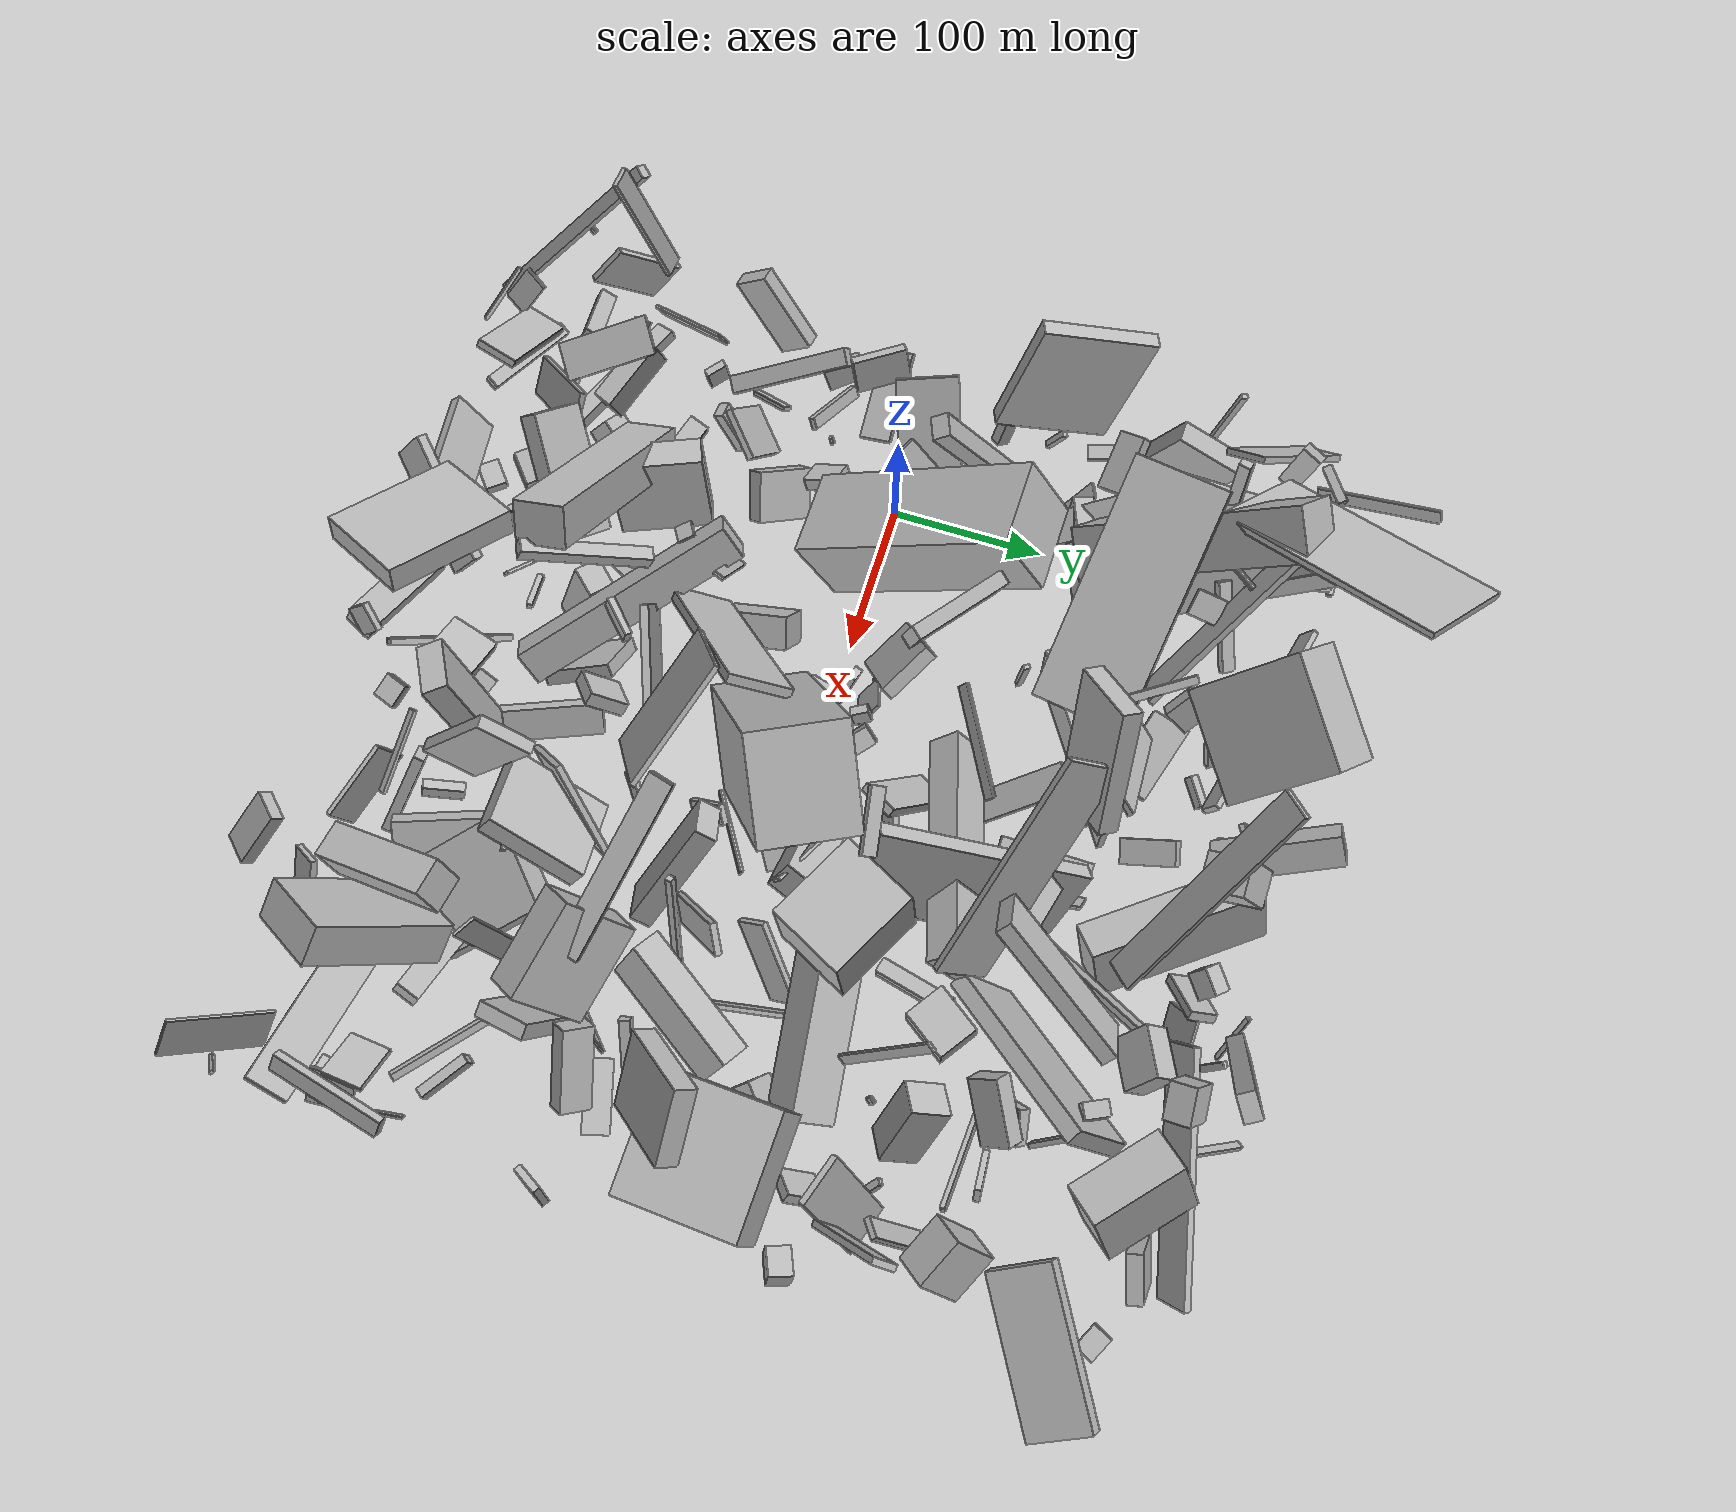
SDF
<sdf version="1.6">
 <world name="default">
  <scene>
   <sky><clouds><speed>12</speed></clouds></sky>
   <ambient>0.4 0.4 0.4 1</ambient>
   <background>0.7 0.7 0.7 1</background>
   <shadows>1</shadows>
  </scene>
  <gravity>0 0 -9.8066</gravity>
  <magnetic_field>6e-06 2.3e-05 -4.2e-05</magnetic_field>
  <physics default="0" name="default_physics" type="ode">
   <ode>
    <solver>
     <type>quick</type>
     <iters>10</iters>
     <sor>1.0</sor>
     <use_dynamic_moi_rescaling>0</use_dynamic_moi_rescaling>
    </solver>
    <constraints>
     <cfm>0</cfm>
     <erp>0.2</erp>
     <contact_max_correcting_vel>100</contact_max_correcting_vel>
     <contact_surface_layer>0.001</contact_surface_layer>
    </constraints>
   </ode>
   <max_step_size>0.004</max_step_size>
   <real_time_factor>1</real_time_factor>
   <real_time_update_rate>250</real_time_update_rate>
  </physics>
  <light name="sun" type="directional">
   <pose>0 0 10 0 0 0</pose>
   <diffuse>0.8 0.8 0.8 1</diffuse>
   <specular>0.2 0.2 0.2 1</specular>
   <attenuation>
    <range>1000</range>
    <constant>0.9</constant>
    <linear>0.01</linear>
    <quadratic>0.001</quadratic>
   </attenuation>
   <direction>-0.5 0.1 -0.9</direction>
  </light>
  <model name="building_1">
   <static>0</static>
   <pose>-5.42810275641664 -239.7220187616653 85.97157220256467 1.3218992795124298 0.7941853755900098 -0.3940899181862939</pose>
   <link name="link">
    <gravity>0</gravity>
    <pose>0 0 13.0 0 0 0</pose>
    <collision name="collision"><geometry><box><size>5 81 26</size></box></geometry></collision>
    <visual name="visual">
     <cast_shadows>0</cast_shadows>
     <geometry><box><size>5 81 26</size></box></geometry>
     <material>
      <script>
       <uri>model://HANNAS_wall/materials/scripts</uri>
       <uri>model://HANNAS_wall/materials/textures</uri>
       <name>vrc/HANNAS_wall</name>
      </script>
     </material>
    </visual>
   </link>
  </model>
  <model name="building_2">
   <static>0</static>
   <pose>-1.69499927644267 78.45073827126195 86.37497318792698 0.07220504103765624 -0.5015056887633661 1.9244864186337203</pose>
   <link name="link">
    <gravity>0</gravity>
    <pose>0 0 57.5 0 0 0</pose>
    <collision name="collision"><geometry><box><size>11 14 115</size></box></geometry></collision>
    <visual name="visual">
     <cast_shadows>0</cast_shadows>
     <geometry><box><size>11 14 115</size></box></geometry>
     <material>
      <script>
       <uri>model://HANNAS_wall/materials/scripts</uri>
       <uri>model://HANNAS_wall/materials/textures</uri>
       <name>vrc/HANNAS_wall</name>
      </script>
     </material>
    </visual>
   </link>
  </model>
  <model name="building_3">
   <static>0</static>
   <pose>196.94101169299068 -23.852186492525295 85.03676326127892 -0.10717618988302265 0.5370241598284978 0.4286737553153996</pose>
   <link name="link">
    <gravity>0</gravity>
    <pose>0 0 75.0 0 0 0</pose>
    <collision name="collision"><geometry><box><size>64 58 150</size></box></geometry></collision>
    <visual name="visual">
     <cast_shadows>0</cast_shadows>
     <geometry><box><size>64 58 150</size></box></geometry>
     <material>
      <script>
       <uri>model://HANNAS_wall/materials/scripts</uri>
       <uri>model://HANNAS_wall/materials/textures</uri>
       <name>vrc/HANNAS_wall</name>
      </script>
     </material>
    </visual>
   </link>
  </model>
  <model name="building_4">
   <static>0</static>
   <pose>246.0392381697584 112.40709381723941 72.94121580072749 0.8314418925521231 -0.8509778097233889 2.696568925000398</pose>
   <link name="link">
    <gravity>0</gravity>
    <pose>0 0 5.5 0 0 0</pose>
    <collision name="collision"><geometry><box><size>59 145 11</size></box></geometry></collision>
    <visual name="visual">
     <cast_shadows>0</cast_shadows>
     <geometry><box><size>59 145 11</size></box></geometry>
     <material>
      <script>
       <uri>model://HANNAS_wall/materials/scripts</uri>
       <uri>model://HANNAS_wall/materials/textures</uri>
       <name>vrc/HANNAS_wall</name>
      </script>
     </material>
    </visual>
   </link>
  </model>
  <model name="building_5">
   <static>0</static>
   <pose>287.5229218052627 213.38739787235647 123.43802710903616 0.73372761388437 0.2270527168911474 -2.3873085260724936</pose>
   <link name="link">
    <gravity>0</gravity>
    <pose>0 0 75.0 0 0 0</pose>
    <collision name="collision"><geometry><box><size>19 4 150</size></box></geometry></collision>
    <visual name="visual">
     <cast_shadows>0</cast_shadows>
     <geometry><box><size>19 4 150</size></box></geometry>
     <material>
      <script>
       <uri>model://HANNAS_wall/materials/scripts</uri>
       <uri>model://HANNAS_wall/materials/textures</uri>
       <name>vrc/HANNAS_wall</name>
      </script>
     </material>
    </visual>
   </link>
  </model>
  <model name="building_6">
   <static>0</static>
   <pose>-4.021483482341315 214.1233752536972 29.090512028109554 -3.027519833887416 -0.9082310783751878 -2.646285269551218</pose>
   <link name="link">
    <gravity>0</gravity>
    <pose>0 0 12.0 0 0 0</pose>
    <collision name="collision"><geometry><box><size>38 73 24</size></box></geometry></collision>
    <visual name="visual">
     <cast_shadows>0</cast_shadows>
     <geometry><box><size>38 73 24</size></box></geometry>
     <material>
      <script>
       <uri>model://HANNAS_wall/materials/scripts</uri>
       <uri>model://HANNAS_wall/materials/textures</uri>
       <name>vrc/HANNAS_wall</name>
      </script>
     </material>
    </visual>
   </link>
  </model>
  <model name="building_7">
   <static>0</static>
   <pose>190.50636840695503 -179.413061214203 63.150342522314716 1.0931903792221618 -0.7215166813194551 -2.0668910434303838</pose>
   <link name="link">
    <gravity>0</gravity>
    <pose>0 0 75.0 0 0 0</pose>
    <collision name="collision"><geometry><box><size>22 21 150</size></box></geometry></collision>
    <visual name="visual">
     <cast_shadows>0</cast_shadows>
     <geometry><box><size>22 21 150</size></box></geometry>
     <material>
      <script>
       <uri>model://HANNAS_wall/materials/scripts</uri>
       <uri>model://HANNAS_wall/materials/textures</uri>
       <name>vrc/HANNAS_wall</name>
      </script>
     </material>
    </visual>
   </link>
  </model>
  <model name="building_8">
   <static>0</static>
   <pose>127.06569472224858 238.69900216793445 95.78885259071888 0.7653650072681788 -0.26575010118467 -2.508618611504383</pose>
   <link name="link">
    <gravity>0</gravity>
    <pose>0 0 37.5 0 0 0</pose>
    <collision name="collision"><geometry><box><size>71 43 75</size></box></geometry></collision>
    <visual name="visual">
     <cast_shadows>0</cast_shadows>
     <geometry><box><size>71 43 75</size></box></geometry>
     <material>
      <script>
       <uri>model://HANNAS_wall/materials/scripts</uri>
       <uri>model://HANNAS_wall/materials/textures</uri>
       <name>vrc/HANNAS_wall</name>
      </script>
     </material>
    </visual>
   </link>
  </model>
  <model name="building_9">
   <static>0</static>
   <pose>33.84589902313799 -151.89104089429046 75.68004075260461 0.3471192922953467 0.7987878249270718 0.28971736532921855</pose>
   <link name="link">
    <gravity>0</gravity>
    <pose>0 0 75.0 0 0 0</pose>
    <collision name="collision"><geometry><box><size>26 32 150</size></box></geometry></collision>
    <visual name="visual">
     <cast_shadows>0</cast_shadows>
     <geometry><box><size>26 32 150</size></box></geometry>
     <material>
      <script>
       <uri>model://HANNAS_wall/materials/scripts</uri>
       <uri>model://HANNAS_wall/materials/textures</uri>
       <name>vrc/HANNAS_wall</name>
      </script>
     </material>
    </visual>
   </link>
  </model>
  <model name="building_10">
   <static>0</static>
   <pose>166.26630641491323 -104.6556512947187 59.05843683317994 -0.4021579293587372 0.0015538447184594562 -1.2440121882095712</pose>
   <link name="link">
    <gravity>0</gravity>
    <pose>0 0 39.5 0 0 0</pose>
    <collision name="collision"><geometry><box><size>5 73 79</size></box></geometry></collision>
    <visual name="visual">
     <cast_shadows>0</cast_shadows>
     <geometry><box><size>5 73 79</size></box></geometry>
     <material>
      <script>
       <uri>model://HANNAS_wall/materials/scripts</uri>
       <uri>model://HANNAS_wall/materials/textures</uri>
       <name>vrc/HANNAS_wall</name>
      </script>
     </material>
    </visual>
   </link>
  </model>
  <model name="building_11">
   <static>0</static>
   <pose>305.34416889173406 286.51877537634414 113.38540585402663 -0.25738495963674096 -0.30998204344259406 -2.5458783594934444</pose>
   <link name="link">
    <gravity>0</gravity>
    <pose>0 0 72.0 0 0 0</pose>
    <collision name="collision"><geometry><box><size>15 10 144</size></box></geometry></collision>
    <visual name="visual">
     <cast_shadows>0</cast_shadows>
     <geometry><box><size>15 10 144</size></box></geometry>
     <material>
      <script>
       <uri>model://HANNAS_wall/materials/scripts</uri>
       <uri>model://HANNAS_wall/materials/textures</uri>
       <name>vrc/HANNAS_wall</name>
      </script>
     </material>
    </visual>
   </link>
  </model>
  <model name="building_12">
   <static>0</static>
   <pose>-64.8675989419472 88.76867121726475 41.04305086515134 1.5485127155446756 0.6728806258827076 1.968441143641871</pose>
   <link name="link">
    <gravity>0</gravity>
    <pose>0 0 2.0 0 0 0</pose>
    <collision name="collision"><geometry><box><size>4 16 4</size></box></geometry></collision>
    <visual name="visual">
     <cast_shadows>0</cast_shadows>
     <geometry><box><size>4 16 4</size></box></geometry>
     <material>
      <script>
       <uri>model://HANNAS_wall/materials/scripts</uri>
       <uri>model://HANNAS_wall/materials/textures</uri>
       <name>vrc/HANNAS_wall</name>
      </script>
     </material>
    </visual>
   </link>
  </model>
  <model name="building_13">
   <static>0</static>
   <pose>264.48225167235995 198.23878747054633 40.77193721252804 1.5332335217083308 0.4482326884495188 -2.51620579279033</pose>
   <link name="link">
    <gravity>0</gravity>
    <pose>0 0 54.5 0 0 0</pose>
    <collision name="collision"><geometry><box><size>26 39 109</size></box></geometry></collision>
    <visual name="visual">
     <cast_shadows>0</cast_shadows>
     <geometry><box><size>26 39 109</size></box></geometry>
     <material>
      <script>
       <uri>model://HANNAS_wall/materials/scripts</uri>
       <uri>model://HANNAS_wall/materials/textures</uri>
       <name>vrc/HANNAS_wall</name>
      </script>
     </material>
    </visual>
   </link>
  </model>
  <model name="building_14">
   <static>0</static>
   <pose>316.0667784874225 -30.431536156151964 60.97014140246682 1.7456314045055163 -0.44665392857538283 -2.6576281017336534</pose>
   <link name="link">
    <gravity>0</gravity>
    <pose>0 0 2.0 0 0 0</pose>
    <collision name="collision"><geometry><box><size>19 113 4</size></box></geometry></collision>
    <visual name="visual">
     <cast_shadows>0</cast_shadows>
     <geometry><box><size>19 113 4</size></box></geometry>
     <material>
      <script>
       <uri>model://HANNAS_wall/materials/scripts</uri>
       <uri>model://HANNAS_wall/materials/textures</uri>
       <name>vrc/HANNAS_wall</name>
      </script>
     </material>
    </visual>
   </link>
  </model>
  <model name="building_15">
   <static>0</static>
   <pose>28.11869566267768 131.06991790489772 89.83151523766983 0.8233377608432507 -0.50299375837068 -2.653175990131853</pose>
   <link name="link">
    <gravity>0</gravity>
    <pose>0 0 75.0 0 0 0</pose>
    <collision name="collision"><geometry><box><size>33 38 150</size></box></geometry></collision>
    <visual name="visual">
     <cast_shadows>0</cast_shadows>
     <geometry><box><size>33 38 150</size></box></geometry>
     <material>
      <script>
       <uri>model://HANNAS_wall/materials/scripts</uri>
       <uri>model://HANNAS_wall/materials/textures</uri>
       <name>vrc/HANNAS_wall</name>
      </script>
     </material>
    </visual>
   </link>
  </model>
  <model name="building_16">
   <static>0</static>
   <pose>392.3072084396442 -132.91633354064174 13.097634788209685 -0.8047364564581748 -0.046846426155950985 -0.7011548754864289</pose>
   <link name="link">
    <gravity>0</gravity>
    <pose>0 0 2.0 0 0 0</pose>
    <collision name="collision"><geometry><box><size>150 5 4</size></box></geometry></collision>
    <visual name="visual">
     <cast_shadows>0</cast_shadows>
     <geometry><box><size>150 5 4</size></box></geometry>
     <material>
      <script>
       <uri>model://HANNAS_wall/materials/scripts</uri>
       <uri>model://HANNAS_wall/materials/textures</uri>
       <name>vrc/HANNAS_wall</name>
      </script>
     </material>
    </visual>
   </link>
  </model>
  <model name="building_17">
   <static>0</static>
   <pose>59.295247222532026 -27.041184664306968 75.38466579360201 0.14372766113227464 -0.9816911505070811 -1.706182812326678</pose>
   <link name="link">
    <gravity>0</gravity>
    <pose>0 0 75.0 0 0 0</pose>
    <collision name="collision"><geometry><box><size>48 55 150</size></box></geometry></collision>
    <visual name="visual">
     <cast_shadows>0</cast_shadows>
     <geometry><box><size>48 55 150</size></box></geometry>
     <material>
      <script>
       <uri>model://HANNAS_wall/materials/scripts</uri>
       <uri>model://HANNAS_wall/materials/textures</uri>
       <name>vrc/HANNAS_wall</name>
      </script>
     </material>
    </visual>
   </link>
  </model>
  <model name="building_18">
   <static>0</static>
   <pose>261.7999692067236 -133.57863174096963 61.57466644306172 0.6465894400426304 0.04952040182783067 2.4536771388072682</pose>
   <link name="link">
    <gravity>0</gravity>
    <pose>0 0 28.5 0 0 0</pose>
    <collision name="collision"><geometry><box><size>4 63 57</size></box></geometry></collision>
    <visual name="visual">
     <cast_shadows>0</cast_shadows>
     <geometry><box><size>4 63 57</size></box></geometry>
     <material>
      <script>
       <uri>model://HANNAS_wall/materials/scripts</uri>
       <uri>model://HANNAS_wall/materials/textures</uri>
       <name>vrc/HANNAS_wall</name>
      </script>
     </material>
    </visual>
   </link>
  </model>
  <model name="building_19">
   <static>0</static>
   <pose>428.0100042955955 -246.20898675549606 37.376018364381196 2.835572647803101 -1.1945118802888808 1.6760327118277407</pose>
   <link name="link">
    <gravity>0</gravity>
    <pose>0 0 14.0 0 0 0</pose>
    <collision name="collision"><geometry><box><size>12 103 28</size></box></geometry></collision>
    <visual name="visual">
     <cast_shadows>0</cast_shadows>
     <geometry><box><size>12 103 28</size></box></geometry>
     <material>
      <script>
       <uri>model://HANNAS_wall/materials/scripts</uri>
       <uri>model://HANNAS_wall/materials/textures</uri>
       <name>vrc/HANNAS_wall</name>
      </script>
     </material>
    </visual>
   </link>
  </model>
  <model name="building_20">
   <static>0</static>
   <pose>395.30493964058525 -92.34229933938144 117.17108386380531 1.0630977818233391 -0.8424706589486903 -1.4455936144356671</pose>
   <link name="link">
    <gravity>0</gravity>
    <pose>0 0 30.5 0 0 0</pose>
    <collision name="collision"><geometry><box><size>51 25 61</size></box></geometry></collision>
    <visual name="visual">
     <cast_shadows>0</cast_shadows>
     <geometry><box><size>51 25 61</size></box></geometry>
     <material>
      <script>
       <uri>model://HANNAS_wall/materials/scripts</uri>
       <uri>model://HANNAS_wall/materials/textures</uri>
       <name>vrc/HANNAS_wall</name>
      </script>
     </material>
    </visual>
   </link>
  </model>
  <model name="building_21">
   <static>0</static>
   <pose>274.1176198754541 -55.66769691245568 55.741877741879144 0.921523315342639 0.4297152876588826 1.5142178881075152</pose>
   <link name="link">
    <gravity>0</gravity>
    <pose>0 0 14.5 0 0 0</pose>
    <collision name="collision"><geometry><box><size>14 82 29</size></box></geometry></collision>
    <visual name="visual">
     <cast_shadows>0</cast_shadows>
     <geometry><box><size>14 82 29</size></box></geometry>
     <material>
      <script>
       <uri>model://HANNAS_wall/materials/scripts</uri>
       <uri>model://HANNAS_wall/materials/textures</uri>
       <name>vrc/HANNAS_wall</name>
      </script>
     </material>
    </visual>
   </link>
  </model>
  <model name="building_22">
   <static>0</static>
   <pose>165.29780434071338 -273.25493520363113 38.56952976451891 0.4997085359125602 1.1886435750374411 -1.4784130958595931</pose>
   <link name="link">
    <gravity>0</gravity>
    <pose>0 0 9.5 0 0 0</pose>
    <collision name="collision"><geometry><box><size>27 67 19</size></box></geometry></collision>
    <visual name="visual">
     <cast_shadows>0</cast_shadows>
     <geometry><box><size>27 67 19</size></box></geometry>
     <material>
      <script>
       <uri>model://HANNAS_wall/materials/scripts</uri>
       <uri>model://HANNAS_wall/materials/textures</uri>
       <name>vrc/HANNAS_wall</name>
      </script>
     </material>
    </visual>
   </link>
  </model>
  <model name="building_23">
   <static>0</static>
   <pose>93.50293925595642 -206.23690654008107 89.42540538922523 2.253204658741233 0.19887257419578286 1.2426885917443982</pose>
   <link name="link">
    <gravity>0</gravity>
    <pose>0 0 2.0 0 0 0</pose>
    <collision name="collision"><geometry><box><size>4 150 4</size></box></geometry></collision>
    <visual name="visual">
     <cast_shadows>0</cast_shadows>
     <geometry><box><size>4 150 4</size></box></geometry>
     <material>
      <script>
       <uri>model://HANNAS_wall/materials/scripts</uri>
       <uri>model://HANNAS_wall/materials/textures</uri>
       <name>vrc/HANNAS_wall</name>
      </script>
     </material>
    </visual>
   </link>
  </model>
  <model name="building_24">
   <static>0</static>
   <pose>141.41804909616135 151.40605957398418 112.35346194942885 -0.09895257340696313 1.0911281022438857 2.890886171830718</pose>
   <link name="link">
    <gravity>0</gravity>
    <pose>0 0 75.0 0 0 0</pose>
    <collision name="collision"><geometry><box><size>13 58 150</size></box></geometry></collision>
    <visual name="visual">
     <cast_shadows>0</cast_shadows>
     <geometry><box><size>13 58 150</size></box></geometry>
     <material>
      <script>
       <uri>model://HANNAS_wall/materials/scripts</uri>
       <uri>model://HANNAS_wall/materials/textures</uri>
       <name>vrc/HANNAS_wall</name>
      </script>
     </material>
    </visual>
   </link>
  </model>
  <model name="building_25">
   <static>0</static>
   <pose>354.780059556248 68.91982962822244 39.401578939200036 0.935533526245235 0.2141554111805798 0.10981015580507866</pose>
   <link name="link">
    <gravity>0</gravity>
    <pose>0 0 15.0 0 0 0</pose>
    <collision name="collision"><geometry><box><size>97 28 30</size></box></geometry></collision>
    <visual name="visual">
     <cast_shadows>0</cast_shadows>
     <geometry><box><size>97 28 30</size></box></geometry>
     <material>
      <script>
       <uri>model://HANNAS_wall/materials/scripts</uri>
       <uri>model://HANNAS_wall/materials/textures</uri>
       <name>vrc/HANNAS_wall</name>
      </script>
     </material>
    </visual>
   </link>
  </model>
  <model name="building_26">
   <static>0</static>
   <pose>447.8451436361768 59.502343330706104 91.80245957601797 1.8022780283147475 0.1440748117896792 -0.04991635219224347</pose>
   <link name="link">
    <gravity>0</gravity>
    <pose>0 0 40.0 0 0 0</pose>
    <collision name="collision"><geometry><box><size>77 32 80</size></box></geometry></collision>
    <visual name="visual">
     <cast_shadows>0</cast_shadows>
     <geometry><box><size>77 32 80</size></box></geometry>
     <material>
      <script>
       <uri>model://HANNAS_wall/materials/scripts</uri>
       <uri>model://HANNAS_wall/materials/textures</uri>
       <name>vrc/HANNAS_wall</name>
      </script>
     </material>
    </visual>
   </link>
  </model>
  <model name="building_27">
   <static>0</static>
   <pose>119.43008749507898 34.0795139759411 62.10818208030938 -2.6143554309659014 -0.9071102201990853 0.5768986253314744</pose>
   <link name="link">
    <gravity>0</gravity>
    <pose>0 0 4.5 0 0 0</pose>
    <collision name="collision"><geometry><box><size>59 37 9</size></box></geometry></collision>
    <visual name="visual">
     <cast_shadows>0</cast_shadows>
     <geometry><box><size>59 37 9</size></box></geometry>
     <material>
      <script>
       <uri>model://HANNAS_wall/materials/scripts</uri>
       <uri>model://HANNAS_wall/materials/textures</uri>
       <name>vrc/HANNAS_wall</name>
      </script>
     </material>
    </visual>
   </link>
  </model>
  <model name="building_28">
   <static>0</static>
   <pose>353.1940645293082 -144.71933570355776 41.332064948987316 -1.4008870746689353 -0.5412063835921306 2.21202912507191</pose>
   <link name="link">
    <gravity>0</gravity>
    <pose>0 0 31.0 0 0 0</pose>
    <collision name="collision"><geometry><box><size>81 19 62</size></box></geometry></collision>
    <visual name="visual">
     <cast_shadows>0</cast_shadows>
     <geometry><box><size>81 19 62</size></box></geometry>
     <material>
      <script>
       <uri>model://HANNAS_wall/materials/scripts</uri>
       <uri>model://HANNAS_wall/materials/textures</uri>
       <name>vrc/HANNAS_wall</name>
      </script>
     </material>
    </visual>
   </link>
  </model>
  <model name="building_29">
   <static>0</static>
   <pose>-18.501599703181732 34.55249805500484 91.51514530621527 -1.599079204548019 -0.7428505819784835 -2.775323332562183</pose>
   <link name="link">
    <gravity>0</gravity>
    <pose>0 0 19.5 0 0 0</pose>
    <collision name="collision"><geometry><box><size>81 4 39</size></box></geometry></collision>
    <visual name="visual">
     <cast_shadows>0</cast_shadows>
     <geometry><box><size>81 4 39</size></box></geometry>
     <material>
      <script>
       <uri>model://HANNAS_wall/materials/scripts</uri>
       <uri>model://HANNAS_wall/materials/textures</uri>
       <name>vrc/HANNAS_wall</name>
      </script>
     </material>
    </visual>
   </link>
  </model>
  <model name="building_30">
   <static>0</static>
   <pose>-51.628188610088806 -85.52173993928845 135.2359919907667 -2.8149377950367485 -0.8573168729308654 -1.9750568537472974</pose>
   <link name="link">
    <gravity>0</gravity>
    <pose>0 0 11.5 0 0 0</pose>
    <collision name="collision"><geometry><box><size>54 10 23</size></box></geometry></collision>
    <visual name="visual">
     <cast_shadows>0</cast_shadows>
     <geometry><box><size>54 10 23</size></box></geometry>
     <material>
      <script>
       <uri>model://HANNAS_wall/materials/scripts</uri>
       <uri>model://HANNAS_wall/materials/textures</uri>
       <name>vrc/HANNAS_wall</name>
      </script>
     </material>
    </visual>
   </link>
  </model>
  <model name="building_31">
   <static>0</static>
   <pose>311.9223770849996 182.14420041256554 138.3061652181933 2.5432250968559402 0.5255048459266045 -0.8384274217295999</pose>
   <link name="link">
    <gravity>0</gravity>
    <pose>0 0 16.5 0 0 0</pose>
    <collision name="collision"><geometry><box><size>10 101 33</size></box></geometry></collision>
    <visual name="visual">
     <cast_shadows>0</cast_shadows>
     <geometry><box><size>10 101 33</size></box></geometry>
     <material>
      <script>
       <uri>model://HANNAS_wall/materials/scripts</uri>
       <uri>model://HANNAS_wall/materials/textures</uri>
       <name>vrc/HANNAS_wall</name>
      </script>
     </material>
    </visual>
   </link>
  </model>
  <model name="building_32">
   <static>0</static>
   <pose>473.5617789788256 121.758763702298 168.416634408525 0.30198070280258865 -0.9400561170758166 1.226183920578841</pose>
   <link name="link">
    <gravity>0</gravity>
    <pose>0 0 7.5 0 0 0</pose>
    <collision name="collision"><geometry><box><size>64 4 15</size></box></geometry></collision>
    <visual name="visual">
     <cast_shadows>0</cast_shadows>
     <geometry><box><size>64 4 15</size></box></geometry>
     <material>
      <script>
       <uri>model://HANNAS_wall/materials/scripts</uri>
       <uri>model://HANNAS_wall/materials/textures</uri>
       <name>vrc/HANNAS_wall</name>
      </script>
     </material>
    </visual>
   </link>
  </model>
  <model name="building_33">
   <static>0</static>
   <pose>146.41188995742405 155.93993946319154 42.02053506550675 0.03514720147749563 0.0022768369842550086 -1.0051173656140224</pose>
   <link name="link">
    <gravity>0</gravity>
    <pose>0 0 21.0 0 0 0</pose>
    <collision name="collision"><geometry><box><size>4 116 42</size></box></geometry></collision>
    <visual name="visual">
     <cast_shadows>0</cast_shadows>
     <geometry><box><size>4 116 42</size></box></geometry>
     <material>
      <script>
       <uri>model://HANNAS_wall/materials/scripts</uri>
       <uri>model://HANNAS_wall/materials/textures</uri>
       <name>vrc/HANNAS_wall</name>
      </script>
     </material>
    </visual>
   </link>
  </model>
  <model name="building_34">
   <static>0</static>
   <pose>-67.7980578442995 217.5691544374693 91.88285674449496 0.8321114528238347 -0.6209963709701257 -2.9994786119582115</pose>
   <link name="link">
    <gravity>0</gravity>
    <pose>0 0 14.0 0 0 0</pose>
    <collision name="collision"><geometry><box><size>4 80 28</size></box></geometry></collision>
    <visual name="visual">
     <cast_shadows>0</cast_shadows>
     <geometry><box><size>4 80 28</size></box></geometry>
     <material>
      <script>
       <uri>model://HANNAS_wall/materials/scripts</uri>
       <uri>model://HANNAS_wall/materials/textures</uri>
       <name>vrc/HANNAS_wall</name>
      </script>
     </material>
    </visual>
   </link>
  </model>
  <model name="building_35">
   <static>0</static>
   <pose>306.7212315610256 127.46683124068255 99.01429808339688 -0.6370680333195952 0.666483974549632 1.9316752935614816</pose>
   <link name="link">
    <gravity>0</gravity>
    <pose>0 0 75.0 0 0 0</pose>
    <collision name="collision"><geometry><box><size>37 4 150</size></box></geometry></collision>
    <visual name="visual">
     <cast_shadows>0</cast_shadows>
     <geometry><box><size>37 4 150</size></box></geometry>
     <material>
      <script>
       <uri>model://HANNAS_wall/materials/scripts</uri>
       <uri>model://HANNAS_wall/materials/textures</uri>
       <name>vrc/HANNAS_wall</name>
      </script>
     </material>
    </visual>
   </link>
  </model>
  <model name="building_36">
   <static>0</static>
   <pose>346.7774181658001 -29.741683877760163 91.44816467800025 1.3407157926723692 0.3816458607613275 2.869380467046199</pose>
   <link name="link">
    <gravity>0</gravity>
    <pose>0 0 2.0 0 0 0</pose>
    <collision name="collision"><geometry><box><size>4 150 4</size></box></geometry></collision>
    <visual name="visual">
     <cast_shadows>0</cast_shadows>
     <geometry><box><size>4 150 4</size></box></geometry>
     <material>
      <script>
       <uri>model://HANNAS_wall/materials/scripts</uri>
       <uri>model://HANNAS_wall/materials/textures</uri>
       <name>vrc/HANNAS_wall</name>
      </script>
     </material>
    </visual>
   </link>
  </model>
  <model name="building_37">
   <static>0</static>
   <pose>166.17992131516675 181.48246720280108 10.305339806930833 -3.0049209529908656 -0.4776856057005283 2.315428261411848</pose>
   <link name="link">
    <gravity>0</gravity>
    <pose>0 0 2.0 0 0 0</pose>
    <collision name="collision"><geometry><box><size>19 5 4</size></box></geometry></collision>
    <visual name="visual">
     <cast_shadows>0</cast_shadows>
     <geometry><box><size>19 5 4</size></box></geometry>
     <material>
      <script>
       <uri>model://HANNAS_wall/materials/scripts</uri>
       <uri>model://HANNAS_wall/materials/textures</uri>
       <name>vrc/HANNAS_wall</name>
      </script>
     </material>
    </visual>
   </link>
  </model>
  <model name="building_38">
   <static>0</static>
   <pose>488.67369343721634 -74.24169819657914 15.866578409388056 0.21499383037150036 -0.07022931389827311 -0.555680839588141</pose>
   <link name="link">
    <gravity>0</gravity>
    <pose>0 0 13.0 0 0 0</pose>
    <collision name="collision"><geometry><box><size>5 19 26</size></box></geometry></collision>
    <visual name="visual">
     <cast_shadows>0</cast_shadows>
     <geometry><box><size>5 19 26</size></box></geometry>
     <material>
      <script>
       <uri>model://HANNAS_wall/materials/scripts</uri>
       <uri>model://HANNAS_wall/materials/textures</uri>
       <name>vrc/HANNAS_wall</name>
      </script>
     </material>
    </visual>
   </link>
  </model>
  <model name="building_39">
   <static>0</static>
   <pose>144.4724974373607 272.6632254772811 8.677053772840171 -1.4650228658175313 0.5666898650434783 -0.9797135430467324</pose>
   <link name="link">
    <gravity>0</gravity>
    <pose>0 0 7.0 0 0 0</pose>
    <collision name="collision"><geometry><box><size>4 14 14</size></box></geometry></collision>
    <visual name="visual">
     <cast_shadows>0</cast_shadows>
     <geometry><box><size>4 14 14</size></box></geometry>
     <material>
      <script>
       <uri>model://HANNAS_wall/materials/scripts</uri>
       <uri>model://HANNAS_wall/materials/textures</uri>
       <name>vrc/HANNAS_wall</name>
      </script>
     </material>
    </visual>
   </link>
  </model>
  <model name="building_40">
   <static>0</static>
   <pose>196.22379663635272 66.03756990982114 44.847923159565646 2.195942374353668 -0.11746353973589373 1.0421103361070279</pose>
   <link name="link">
    <gravity>0</gravity>
    <pose>0 0 3.0 0 0 0</pose>
    <collision name="collision"><geometry><box><size>24 70 6</size></box></geometry></collision>
    <visual name="visual">
     <cast_shadows>0</cast_shadows>
     <geometry><box><size>24 70 6</size></box></geometry>
     <material>
      <script>
       <uri>model://HANNAS_wall/materials/scripts</uri>
       <uri>model://HANNAS_wall/materials/textures</uri>
       <name>vrc/HANNAS_wall</name>
      </script>
     </material>
    </visual>
   </link>
  </model>
  <model name="building_41">
   <static>0</static>
   <pose>-16.573700804806165 -211.18111668127642 28.42816205441622 -0.2508484192820783 1.3294683724410303 0.9418321327773401</pose>
   <link name="link">
    <gravity>0</gravity>
    <pose>0 0 6.5 0 0 0</pose>
    <collision name="collision"><geometry><box><size>7 124 13</size></box></geometry></collision>
    <visual name="visual">
     <cast_shadows>0</cast_shadows>
     <geometry><box><size>7 124 13</size></box></geometry>
     <material>
      <script>
       <uri>model://HANNAS_wall/materials/scripts</uri>
       <uri>model://HANNAS_wall/materials/textures</uri>
       <name>vrc/HANNAS_wall</name>
      </script>
     </material>
    </visual>
   </link>
  </model>
  <model name="building_42">
   <static>0</static>
   <pose>413.5281500367438 251.74328512992653 162.5584119064588 0.42518302474043196 0.08525247721073136 -0.7349285900145905</pose>
   <link name="link">
    <gravity>0</gravity>
    <pose>0 0 21.5 0 0 0</pose>
    <collision name="collision"><geometry><box><size>54 26 43</size></box></geometry></collision>
    <visual name="visual">
     <cast_shadows>0</cast_shadows>
     <geometry><box><size>54 26 43</size></box></geometry>
     <material>
      <script>
       <uri>model://HANNAS_wall/materials/scripts</uri>
       <uri>model://HANNAS_wall/materials/textures</uri>
       <name>vrc/HANNAS_wall</name>
      </script>
     </material>
    </visual>
   </link>
  </model>
  <model name="building_43">
   <static>0</static>
   <pose>35.012057612316056 225.5107082541949 53.2711031528598 0.8115681893532596 -0.7263582766795112 0.35663448138038545</pose>
   <link name="link">
    <gravity>0</gravity>
    <pose>0 0 2.0 0 0 0</pose>
    <collision name="collision"><geometry><box><size>23 135 4</size></box></geometry></collision>
    <visual name="visual">
     <cast_shadows>0</cast_shadows>
     <geometry><box><size>23 135 4</size></box></geometry>
     <material>
      <script>
       <uri>model://HANNAS_wall/materials/scripts</uri>
       <uri>model://HANNAS_wall/materials/textures</uri>
       <name>vrc/HANNAS_wall</name>
      </script>
     </material>
    </visual>
   </link>
  </model>
  <model name="building_44">
   <static>0</static>
   <pose>65.28228357495722 -133.36924564193194 45.98189960271765 -0.17454358389254931 -0.036807849850491584 1.942890977357294</pose>
   <link name="link">
    <gravity>0</gravity>
    <pose>0 0 33.0 0 0 0</pose>
    <collision name="collision"><geometry><box><size>58 18 66</size></box></geometry></collision>
    <visual name="visual">
     <cast_shadows>0</cast_shadows>
     <geometry><box><size>58 18 66</size></box></geometry>
     <material>
      <script>
       <uri>model://HANNAS_wall/materials/scripts</uri>
       <uri>model://HANNAS_wall/materials/textures</uri>
       <name>vrc/HANNAS_wall</name>
      </script>
     </material>
    </visual>
   </link>
  </model>
  <model name="building_45">
   <static>0</static>
   <pose>322.1054726729883 -67.02097377802386 168.16520493836197 3.118902541991762 0.5134133669927164 -0.2839396074568285</pose>
   <link name="link">
    <gravity>0</gravity>
    <pose>0 0 2.0 0 0 0</pose>
    <collision name="collision"><geometry><box><size>115 15 4</size></box></geometry></collision>
    <visual name="visual">
     <cast_shadows>0</cast_shadows>
     <geometry><box><size>115 15 4</size></box></geometry>
     <material>
      <script>
       <uri>model://HANNAS_wall/materials/scripts</uri>
       <uri>model://HANNAS_wall/materials/textures</uri>
       <name>vrc/HANNAS_wall</name>
      </script>
     </material>
    </visual>
   </link>
  </model>
  <model name="building_46">
   <static>0</static>
   <pose>409.81647661095 -33.12656830785072 84.91780740882496 0.6727454625095052 -0.655723175859762 3.1279728697994766</pose>
   <link name="link">
    <gravity>0</gravity>
    <pose>0 0 31.0 0 0 0</pose>
    <collision name="collision"><geometry><box><size>50 14 62</size></box></geometry></collision>
    <visual name="visual">
     <cast_shadows>0</cast_shadows>
     <geometry><box><size>50 14 62</size></box></geometry>
     <material>
      <script>
       <uri>model://HANNAS_wall/materials/scripts</uri>
       <uri>model://HANNAS_wall/materials/textures</uri>
       <name>vrc/HANNAS_wall</name>
      </script>
     </material>
    </visual>
   </link>
  </model>
  <model name="building_47">
   <static>0</static>
   <pose>282.3333516618749 206.32558568765282 60.27367444680189 -0.6378160163743561 -0.8135453570839897 -1.7786275774059461</pose>
   <link name="link">
    <gravity>0</gravity>
    <pose>0 0 6.5 0 0 0</pose>
    <collision name="collision"><geometry><box><size>150 4 13</size></box></geometry></collision>
    <visual name="visual">
     <cast_shadows>0</cast_shadows>
     <geometry><box><size>150 4 13</size></box></geometry>
     <material>
      <script>
       <uri>model://HANNAS_wall/materials/scripts</uri>
       <uri>model://HANNAS_wall/materials/textures</uri>
       <name>vrc/HANNAS_wall</name>
      </script>
     </material>
    </visual>
   </link>
  </model>
  <model name="building_48">
   <static>0</static>
   <pose>372.65005872697157 -219.85057853060357 116.85582710702974 -0.9303031945038349 -0.8128402908479886 -1.0077503251969608</pose>
   <link name="link">
    <gravity>0</gravity>
    <pose>0 0 24.5 0 0 0</pose>
    <collision name="collision"><geometry><box><size>90 25 49</size></box></geometry></collision>
    <visual name="visual">
     <cast_shadows>0</cast_shadows>
     <geometry><box><size>90 25 49</size></box></geometry>
     <material>
      <script>
       <uri>model://HANNAS_wall/materials/scripts</uri>
       <uri>model://HANNAS_wall/materials/textures</uri>
       <name>vrc/HANNAS_wall</name>
      </script>
     </material>
    </visual>
   </link>
  </model>
  <model name="building_49">
   <static>0</static>
   <pose>162.9117258286655 196.43203059050646 95.68860959035601 0.7536693604486843 -0.583079489147361 -0.0154469404742837</pose>
   <link name="link">
    <gravity>0</gravity>
    <pose>0 0 20.0 0 0 0</pose>
    <collision name="collision"><geometry><box><size>74 4 40</size></box></geometry></collision>
    <visual name="visual">
     <cast_shadows>0</cast_shadows>
     <geometry><box><size>74 4 40</size></box></geometry>
     <material>
      <script>
       <uri>model://HANNAS_wall/materials/scripts</uri>
       <uri>model://HANNAS_wall/materials/textures</uri>
       <name>vrc/HANNAS_wall</name>
      </script>
     </material>
    </visual>
   </link>
  </model>
  <model name="building_50">
   <static>0</static>
   <pose>220.86505331360195 -256.19160992129406 146.92379286603537 -2.2550753702309385 -0.8256295268816202 1.6528478169733016</pose>
   <link name="link">
    <gravity>0</gravity>
    <pose>0 0 2.0 0 0 0</pose>
    <collision name="collision"><geometry><box><size>17 17 4</size></box></geometry></collision>
    <visual name="visual">
     <cast_shadows>0</cast_shadows>
     <geometry><box><size>17 17 4</size></box></geometry>
     <material>
      <script>
       <uri>model://HANNAS_wall/materials/scripts</uri>
       <uri>model://HANNAS_wall/materials/textures</uri>
       <name>vrc/HANNAS_wall</name>
      </script>
     </material>
    </visual>
   </link>
  </model>
  <model name="building_51">
   <static>0</static>
   <pose>-62.80150090943144 -35.108215530397416 35.73823834480329 1.2864220787834153 -0.27170431004789664 -3.119014227257547</pose>
   <link name="link">
    <gravity>0</gravity>
    <pose>0 0 10.5 0 0 0</pose>
    <collision name="collision"><geometry><box><size>60 4 21</size></box></geometry></collision>
    <visual name="visual">
     <cast_shadows>0</cast_shadows>
     <geometry><box><size>60 4 21</size></box></geometry>
     <material>
      <script>
       <uri>model://HANNAS_wall/materials/scripts</uri>
       <uri>model://HANNAS_wall/materials/textures</uri>
       <name>vrc/HANNAS_wall</name>
      </script>
     </material>
    </visual>
   </link>
  </model>
  <model name="building_52">
   <static>0</static>
   <pose>260.45096502845166 31.132917213910975 47.480260439311145 1.1229656785537947 -0.6097243819232256 -0.043908216196138904</pose>
   <link name="link">
    <gravity>0</gravity>
    <pose>0 0 12.0 0 0 0</pose>
    <collision name="collision"><geometry><box><size>54 21 24</size></box></geometry></collision>
    <visual name="visual">
     <cast_shadows>0</cast_shadows>
     <geometry><box><size>54 21 24</size></box></geometry>
     <material>
      <script>
       <uri>model://HANNAS_wall/materials/scripts</uri>
       <uri>model://HANNAS_wall/materials/textures</uri>
       <name>vrc/HANNAS_wall</name>
      </script>
     </material>
    </visual>
   </link>
  </model>
  <model name="building_53">
   <static>0</static>
   <pose>134.84612491259455 -160.10815783810872 34.6635390487251 1.4158742561633624 -0.22493966590599784 -0.703948774160974</pose>
   <link name="link">
    <gravity>0</gravity>
    <pose>0 0 9.5 0 0 0</pose>
    <collision name="collision"><geometry><box><size>17 63 19</size></box></geometry></collision>
    <visual name="visual">
     <cast_shadows>0</cast_shadows>
     <geometry><box><size>17 63 19</size></box></geometry>
     <material>
      <script>
       <uri>model://HANNAS_wall/materials/scripts</uri>
       <uri>model://HANNAS_wall/materials/textures</uri>
       <name>vrc/HANNAS_wall</name>
      </script>
     </material>
    </visual>
   </link>
  </model>
  <model name="building_54">
   <static>0</static>
   <pose>265.6957070730981 -153.7687922476667 13.620396007652708 1.9270283446784517 0.3181062293003859 2.5058402378850833</pose>
   <link name="link">
    <gravity>0</gravity>
    <pose>0 0 2.0 0 0 0</pose>
    <collision name="collision"><geometry><box><size>38 5 4</size></box></geometry></collision>
    <visual name="visual">
     <cast_shadows>0</cast_shadows>
     <geometry><box><size>38 5 4</size></box></geometry>
     <material>
      <script>
       <uri>model://HANNAS_wall/materials/scripts</uri>
       <uri>model://HANNAS_wall/materials/textures</uri>
       <name>vrc/HANNAS_wall</name>
      </script>
     </material>
    </visual>
   </link>
  </model>
  <model name="building_55">
   <static>0</static>
   <pose>348.7555725041409 -272.2305155143253 126.04868505978634 -0.248468402914568 -0.7291242090016277 2.547190054884107</pose>
   <link name="link">
    <gravity>0</gravity>
    <pose>0 0 4.0 0 0 0</pose>
    <collision name="collision"><geometry><box><size>39 20 8</size></box></geometry></collision>
    <visual name="visual">
     <cast_shadows>0</cast_shadows>
     <geometry><box><size>39 20 8</size></box></geometry>
     <material>
      <script>
       <uri>model://HANNAS_wall/materials/scripts</uri>
       <uri>model://HANNAS_wall/materials/textures</uri>
       <name>vrc/HANNAS_wall</name>
      </script>
     </material>
    </visual>
   </link>
  </model>
  <model name="building_56">
   <static>0</static>
   <pose>353.1146900377908 229.15745046192978 81.06606824895431 1.6246591654610778 0.09088854913317261 0.43664834529230867</pose>
   <link name="link">
    <gravity>0</gravity>
    <pose>0 0 7.5 0 0 0</pose>
    <collision name="collision"><geometry><box><size>10 28 15</size></box></geometry></collision>
    <visual name="visual">
     <cast_shadows>0</cast_shadows>
     <geometry><box><size>10 28 15</size></box></geometry>
     <material>
      <script>
       <uri>model://HANNAS_wall/materials/scripts</uri>
       <uri>model://HANNAS_wall/materials/textures</uri>
       <name>vrc/HANNAS_wall</name>
      </script>
     </material>
    </visual>
   </link>
  </model>
  <model name="building_57">
   <static>0</static>
   <pose>372.8397094920472 229.54579999024057 72.28215962919838 2.254910144712333 -1.003458802321089 -1.3164508423487904</pose>
   <link name="link">
    <gravity>0</gravity>
    <pose>0 0 61.5 0 0 0</pose>
    <collision name="collision"><geometry><box><size>59 11 123</size></box></geometry></collision>
    <visual name="visual">
     <cast_shadows>0</cast_shadows>
     <geometry><box><size>59 11 123</size></box></geometry>
     <material>
      <script>
       <uri>model://HANNAS_wall/materials/scripts</uri>
       <uri>model://HANNAS_wall/materials/textures</uri>
       <name>vrc/HANNAS_wall</name>
      </script>
     </material>
    </visual>
   </link>
  </model>
  <model name="building_58">
   <static>0</static>
   <pose>25.721043345929715 34.76046443924251 19.42309811803009 0.7407969602970624 -0.19065259778635846 -1.9637620691150814</pose>
   <link name="link">
    <gravity>0</gravity>
    <pose>0 0 10.0 0 0 0</pose>
    <collision name="collision"><geometry><box><size>13 27 20</size></box></geometry></collision>
    <visual name="visual">
     <cast_shadows>0</cast_shadows>
     <geometry><box><size>13 27 20</size></box></geometry>
     <material>
      <script>
       <uri>model://HANNAS_wall/materials/scripts</uri>
       <uri>model://HANNAS_wall/materials/textures</uri>
       <name>vrc/HANNAS_wall</name>
      </script>
     </material>
    </visual>
   </link>
  </model>
  <model name="building_59">
   <static>0</static>
   <pose>-46.795529385791674 -58.26615661997201 32.13460712737607 0.6069768328617062 -0.8266439071850114 -2.428429025390064</pose>
   <link name="link">
    <gravity>0</gravity>
    <pose>0 0 2.0 0 0 0</pose>
    <collision name="collision"><geometry><box><size>8 47 4</size></box></geometry></collision>
    <visual name="visual">
     <cast_shadows>0</cast_shadows>
     <geometry><box><size>8 47 4</size></box></geometry>
     <material>
      <script>
       <uri>model://HANNAS_wall/materials/scripts</uri>
       <uri>model://HANNAS_wall/materials/textures</uri>
       <name>vrc/HANNAS_wall</name>
      </script>
     </material>
    </visual>
   </link>
  </model>
  <model name="building_60">
   <static>0</static>
   <pose>-55.246284490398345 -52.67597682796404 70.52888772277947 1.0408543811598965 -0.18750298344435254 2.1800897783020736</pose>
   <link name="link">
    <gravity>0</gravity>
    <pose>0 0 2.0 0 0 0</pose>
    <collision name="collision"><geometry><box><size>25 17 4</size></box></geometry></collision>
    <visual name="visual">
     <cast_shadows>0</cast_shadows>
     <geometry><box><size>25 17 4</size></box></geometry>
     <material>
      <script>
       <uri>model://HANNAS_wall/materials/scripts</uri>
       <uri>model://HANNAS_wall/materials/textures</uri>
       <name>vrc/HANNAS_wall</name>
      </script>
     </material>
    </visual>
   </link>
  </model>
  <model name="building_61">
   <static>0</static>
   <pose>454.4455979796617 157.19957674618342 95.64992392870477 -0.5362597075483604 -0.8630973474018058 -1.589940140255707</pose>
   <link name="link">
    <gravity>0</gravity>
    <pose>0 0 11.5 0 0 0</pose>
    <collision name="collision"><geometry><box><size>33 32 23</size></box></geometry></collision>
    <visual name="visual">
     <cast_shadows>0</cast_shadows>
     <geometry><box><size>33 32 23</size></box></geometry>
     <material>
      <script>
       <uri>model://HANNAS_wall/materials/scripts</uri>
       <uri>model://HANNAS_wall/materials/textures</uri>
       <name>vrc/HANNAS_wall</name>
      </script>
     </material>
    </visual>
   </link>
  </model>
  <model name="building_62">
   <static>0</static>
   <pose>-17.448397632257553 132.29022130972038 42.665629059918814 -0.29540694255753763 0.4982888660459151 -1.2260390385102544</pose>
   <link name="link">
    <gravity>0</gravity>
    <pose>0 0 2.0 0 0 0</pose>
    <collision name="collision"><geometry><box><size>106 21 4</size></box></geometry></collision>
    <visual name="visual">
     <cast_shadows>0</cast_shadows>
     <geometry><box><size>106 21 4</size></box></geometry>
     <material>
      <script>
       <uri>model://HANNAS_wall/materials/scripts</uri>
       <uri>model://HANNAS_wall/materials/textures</uri>
       <name>vrc/HANNAS_wall</name>
      </script>
     </material>
    </visual>
   </link>
  </model>
  <model name="building_63">
   <static>0</static>
   <pose>129.72382476370478 -216.8122920937503 152.89608224947602 -1.2462023191349325 0.36279655640454006 -2.060488606820153</pose>
   <link name="link">
    <gravity>0</gravity>
    <pose>0 0 40.5 0 0 0</pose>
    <collision name="collision"><geometry><box><size>65 15 81</size></box></geometry></collision>
    <visual name="visual">
     <cast_shadows>0</cast_shadows>
     <geometry><box><size>65 15 81</size></box></geometry>
     <material>
      <script>
       <uri>model://HANNAS_wall/materials/scripts</uri>
       <uri>model://HANNAS_wall/materials/textures</uri>
       <name>vrc/HANNAS_wall</name>
      </script>
     </material>
    </visual>
   </link>
  </model>
  <model name="building_64">
   <static>0</static>
   <pose>301.7135998658954 262.4967223012218 66.36645070043379 2.351691197250459 -1.1669851162304328 1.0849620932479414</pose>
   <link name="link">
    <gravity>0</gravity>
    <pose>0 0 75.0 0 0 0</pose>
    <collision name="collision"><geometry><box><size>36 4 150</size></box></geometry></collision>
    <visual name="visual">
     <cast_shadows>0</cast_shadows>
     <geometry><box><size>36 4 150</size></box></geometry>
     <material>
      <script>
       <uri>model://HANNAS_wall/materials/scripts</uri>
       <uri>model://HANNAS_wall/materials/textures</uri>
       <name>vrc/HANNAS_wall</name>
      </script>
     </material>
    </visual>
   </link>
  </model>
  <model name="building_65">
   <static>0</static>
   <pose>385.9157158319795 136.11774128148485 46.58962567178883 1.1092816661097866 -0.4267034483785469 0.4796998627245925</pose>
   <link name="link">
    <gravity>0</gravity>
    <pose>0 0 12.5 0 0 0</pose>
    <collision name="collision"><geometry><box><size>22 49 25</size></box></geometry></collision>
    <visual name="visual">
     <cast_shadows>0</cast_shadows>
     <geometry><box><size>22 49 25</size></box></geometry>
     <material>
      <script>
       <uri>model://HANNAS_wall/materials/scripts</uri>
       <uri>model://HANNAS_wall/materials/textures</uri>
       <name>vrc/HANNAS_wall</name>
      </script>
     </material>
    </visual>
   </link>
  </model>
  <model name="building_66">
   <static>0</static>
   <pose>159.95848529587977 86.50468496385342 46.68314994798267 1.195446878900916 0.8605179694929719 1.5425542920536692</pose>
   <link name="link">
    <gravity>0</gravity>
    <pose>0 0 75.0 0 0 0</pose>
    <collision name="collision"><geometry><box><size>28 21 150</size></box></geometry></collision>
    <visual name="visual">
     <cast_shadows>0</cast_shadows>
     <geometry><box><size>28 21 150</size></box></geometry>
     <material>
      <script>
       <uri>model://HANNAS_wall/materials/scripts</uri>
       <uri>model://HANNAS_wall/materials/textures</uri>
       <name>vrc/HANNAS_wall</name>
      </script>
     </material>
    </visual>
   </link>
  </model>
  <model name="building_67">
   <static>0</static>
   <pose>117.41643131386455 190.6665363558045 19.630085070958124 -1.8713272717616756 -1.2817797715934394 0.009358426451447863</pose>
   <link name="link">
    <gravity>0</gravity>
    <pose>0 0 12.5 0 0 0</pose>
    <collision name="collision"><geometry><box><size>18 51 25</size></box></geometry></collision>
    <visual name="visual">
     <cast_shadows>0</cast_shadows>
     <geometry><box><size>18 51 25</size></box></geometry>
     <material>
      <script>
       <uri>model://HANNAS_wall/materials/scripts</uri>
       <uri>model://HANNAS_wall/materials/textures</uri>
       <name>vrc/HANNAS_wall</name>
      </script>
     </material>
    </visual>
   </link>
  </model>
  <model name="building_68">
   <static>0</static>
   <pose>133.68899683344443 -201.15921752342024 28.12577484494996 0.25896905218363564 0.0042694306786999646 -1.496652786326828</pose>
   <link name="link">
    <gravity>0</gravity>
    <pose>0 0 2.0 0 0 0</pose>
    <collision name="collision"><geometry><box><size>4 25 4</size></box></geometry></collision>
    <visual name="visual">
     <cast_shadows>0</cast_shadows>
     <geometry><box><size>4 25 4</size></box></geometry>
     <material>
      <script>
       <uri>model://HANNAS_wall/materials/scripts</uri>
       <uri>model://HANNAS_wall/materials/textures</uri>
       <name>vrc/HANNAS_wall</name>
      </script>
     </material>
    </visual>
   </link>
  </model>
  <model name="building_69">
   <static>0</static>
   <pose>436.08399933277644 271.3796080361466 45.21805190600404 -2.664721027043559 -0.257553861634617 1.7644111512376273</pose>
   <link name="link">
    <gravity>0</gravity>
    <pose>0 0 16.5 0 0 0</pose>
    <collision name="collision"><geometry><box><size>10 31 33</size></box></geometry></collision>
    <visual name="visual">
     <cast_shadows>0</cast_shadows>
     <geometry><box><size>10 31 33</size></box></geometry>
     <material>
      <script>
       <uri>model://HANNAS_wall/materials/scripts</uri>
       <uri>model://HANNAS_wall/materials/textures</uri>
       <name>vrc/HANNAS_wall</name>
      </script>
     </material>
    </visual>
   </link>
  </model>
  <model name="building_70">
   <static>0</static>
   <pose>46.779562184224886 143.21849398432911 31.919280016706143 1.660437688073315 -0.08180928195174933 -1.2226653690119238</pose>
   <link name="link">
    <gravity>0</gravity>
    <pose>0 0 39.0 0 0 0</pose>
    <collision name="collision"><geometry><box><size>13 36 78</size></box></geometry></collision>
    <visual name="visual">
     <cast_shadows>0</cast_shadows>
     <geometry><box><size>13 36 78</size></box></geometry>
     <material>
      <script>
       <uri>model://HANNAS_wall/materials/scripts</uri>
       <uri>model://HANNAS_wall/materials/textures</uri>
       <name>vrc/HANNAS_wall</name>
      </script>
     </material>
    </visual>
   </link>
  </model>
  <model name="building_71">
   <static>0</static>
   <pose>437.3565216037048 -68.61914271934508 34.30843877381673 -0.8928832874892836 0.47854132627180146 2.137817232400987</pose>
   <link name="link">
    <gravity>0</gravity>
    <pose>0 0 26.5 0 0 0</pose>
    <collision name="collision"><geometry><box><size>20 14 53</size></box></geometry></collision>
    <visual name="visual">
     <cast_shadows>0</cast_shadows>
     <geometry><box><size>20 14 53</size></box></geometry>
     <material>
      <script>
       <uri>model://HANNAS_wall/materials/scripts</uri>
       <uri>model://HANNAS_wall/materials/textures</uri>
       <name>vrc/HANNAS_wall</name>
      </script>
     </material>
    </visual>
   </link>
  </model>
  <model name="building_72">
   <static>0</static>
   <pose>454.28340206718485 117.21335669131878 44.15490676215887 -0.030163057962086556 -0.4453551707273067 1.2679857277166433</pose>
   <link name="link">
    <gravity>0</gravity>
    <pose>0 0 38.5 0 0 0</pose>
    <collision name="collision"><geometry><box><size>4 32 77</size></box></geometry></collision>
    <visual name="visual">
     <cast_shadows>0</cast_shadows>
     <geometry><box><size>4 32 77</size></box></geometry>
     <material>
      <script>
       <uri>model://HANNAS_wall/materials/scripts</uri>
       <uri>model://HANNAS_wall/materials/textures</uri>
       <name>vrc/HANNAS_wall</name>
      </script>
     </material>
    </visual>
   </link>
  </model>
  <model name="building_73">
   <static>0</static>
   <pose>314.17992808929654 -126.4035847208243 107.84374916059397 2.230889309847016 0.8909190472969664 -0.939733376667284</pose>
   <link name="link">
    <gravity>0</gravity>
    <pose>0 0 26.5 0 0 0</pose>
    <collision name="collision"><geometry><box><size>15 64 53</size></box></geometry></collision>
    <visual name="visual">
     <cast_shadows>0</cast_shadows>
     <geometry><box><size>15 64 53</size></box></geometry>
     <material>
      <script>
       <uri>model://HANNAS_wall/materials/scripts</uri>
       <uri>model://HANNAS_wall/materials/textures</uri>
       <name>vrc/HANNAS_wall</name>
      </script>
     </material>
    </visual>
   </link>
  </model>
  <model name="building_74">
   <static>0</static>
   <pose>5.640465864170977 -228.60789635987018 51.6064259739527 2.228034573761285 0.5392966152699268 -2.2523121590061224</pose>
   <link name="link">
    <gravity>0</gravity>
    <pose>0 0 2.0 0 0 0</pose>
    <collision name="collision"><geometry><box><size>63 26 4</size></box></geometry></collision>
    <visual name="visual">
     <cast_shadows>0</cast_shadows>
     <geometry><box><size>63 26 4</size></box></geometry>
     <material>
      <script>
       <uri>model://HANNAS_wall/materials/scripts</uri>
       <uri>model://HANNAS_wall/materials/textures</uri>
       <name>vrc/HANNAS_wall</name>
      </script>
     </material>
    </visual>
   </link>
  </model>
  <model name="building_75">
   <static>0</static>
   <pose>188.74963731434354 -107.0743389491158 186.80692967861177 2.879050373058401 0.030683555929073732 0.7590617573124923</pose>
   <link name="link">
    <gravity>0</gravity>
    <pose>0 0 4.5 0 0 0</pose>
    <collision name="collision"><geometry><box><size>24 4 9</size></box></geometry></collision>
    <visual name="visual">
     <cast_shadows>0</cast_shadows>
     <geometry><box><size>24 4 9</size></box></geometry>
     <material>
      <script>
       <uri>model://HANNAS_wall/materials/scripts</uri>
       <uri>model://HANNAS_wall/materials/textures</uri>
       <name>vrc/HANNAS_wall</name>
      </script>
     </material>
    </visual>
   </link>
  </model>
  <model name="building_76">
   <static>0</static>
   <pose>399.0767223659126 -16.141876456013794 6.560536453187842 -2.8326186868595746 0.6589390769807529 -1.0916643457401227</pose>
   <link name="link">
    <gravity>0</gravity>
    <pose>0 0 4.0 0 0 0</pose>
    <collision name="collision"><geometry><box><size>4 10 8</size></box></geometry></collision>
    <visual name="visual">
     <cast_shadows>0</cast_shadows>
     <geometry><box><size>4 10 8</size></box></geometry>
     <material>
      <script>
       <uri>model://HANNAS_wall/materials/scripts</uri>
       <uri>model://HANNAS_wall/materials/textures</uri>
       <name>vrc/HANNAS_wall</name>
      </script>
     </material>
    </visual>
   </link>
  </model>
  <model name="building_77">
   <static>0</static>
   <pose>-71.95500102650558 -236.8877465087458 124.16990555256365 -2.0856577003965104 0.8538065257584017 -1.15359892929485</pose>
   <link name="link">
    <gravity>0</gravity>
    <pose>0 0 4.0 0 0 0</pose>
    <collision name="collision"><geometry><box><size>150 7 8</size></box></geometry></collision>
    <visual name="visual">
     <cast_shadows>0</cast_shadows>
     <geometry><box><size>150 7 8</size></box></geometry>
     <material>
      <script>
       <uri>model://HANNAS_wall/materials/scripts</uri>
       <uri>model://HANNAS_wall/materials/textures</uri>
       <name>vrc/HANNAS_wall</name>
      </script>
     </material>
    </visual>
   </link>
  </model>
  <model name="building_78">
   <static>0</static>
   <pose>99.06335493038986 248.19953153566237 20.985868171813188 -1.4310898031696784 0.5209758179994876 -2.3997343403403955</pose>
   <link name="link">
    <gravity>0</gravity>
    <pose>0 0 8.0 0 0 0</pose>
    <collision name="collision"><geometry><box><size>5 25 16</size></box></geometry></collision>
    <visual name="visual">
     <cast_shadows>0</cast_shadows>
     <geometry><box><size>5 25 16</size></box></geometry>
     <material>
      <script>
       <uri>model://HANNAS_wall/materials/scripts</uri>
       <uri>model://HANNAS_wall/materials/textures</uri>
       <name>vrc/HANNAS_wall</name>
      </script>
     </material>
    </visual>
   </link>
  </model>
  <model name="building_79">
   <static>0</static>
   <pose>319.658312011298 -225.1948068855677 32.17056919056798 -1.6711283728660589 0.7099019607687979 0.2992518365790529</pose>
   <link name="link">
    <gravity>0</gravity>
    <pose>0 0 43.0 0 0 0</pose>
    <collision name="collision"><geometry><box><size>40 12 86</size></box></geometry></collision>
    <visual name="visual">
     <cast_shadows>0</cast_shadows>
     <geometry><box><size>40 12 86</size></box></geometry>
     <material>
      <script>
       <uri>model://HANNAS_wall/materials/scripts</uri>
       <uri>model://HANNAS_wall/materials/textures</uri>
       <name>vrc/HANNAS_wall</name>
      </script>
     </material>
    </visual>
   </link>
  </model>
  <model name="building_80">
   <static>0</static>
   <pose>80.53274626531588 265.13773406668054 26.249005241027668 1.1041793027183076 -0.19085600257091656 -0.24006480871131267</pose>
   <link name="link">
    <gravity>0</gravity>
    <pose>0 0 2.0 0 0 0</pose>
    <collision name="collision"><geometry><box><size>150 14 4</size></box></geometry></collision>
    <visual name="visual">
     <cast_shadows>0</cast_shadows>
     <geometry><box><size>150 14 4</size></box></geometry>
     <material>
      <script>
       <uri>model://HANNAS_wall/materials/scripts</uri>
       <uri>model://HANNAS_wall/materials/textures</uri>
       <name>vrc/HANNAS_wall</name>
      </script>
     </material>
    </visual>
   </link>
  </model>
  <model name="building_81">
   <static>0</static>
   <pose>282.7691883716138 -228.78588431570282 30.869368836469384 -1.1628829469563158 -0.7679619171296312 2.7771609967227593</pose>
   <link name="link">
    <gravity>0</gravity>
    <pose>0 0 3.5 0 0 0</pose>
    <collision name="collision"><geometry><box><size>59 14 7</size></box></geometry></collision>
    <visual name="visual">
     <cast_shadows>0</cast_shadows>
     <geometry><box><size>59 14 7</size></box></geometry>
     <material>
      <script>
       <uri>model://HANNAS_wall/materials/scripts</uri>
       <uri>model://HANNAS_wall/materials/textures</uri>
       <name>vrc/HANNAS_wall</name>
      </script>
     </material>
    </visual>
   </link>
  </model>
  <model name="building_82">
   <static>0</static>
   <pose>402.45997569483455 -41.48999578687453 32.10347523463004 1.777138436853245 0.6306036400377316 0.33222855502667137</pose>
   <link name="link">
    <gravity>0</gravity>
    <pose>0 0 3.5 0 0 0</pose>
    <collision name="collision"><geometry><box><size>60 6 7</size></box></geometry></collision>
    <visual name="visual">
     <cast_shadows>0</cast_shadows>
     <geometry><box><size>60 6 7</size></box></geometry>
     <material>
      <script>
       <uri>model://HANNAS_wall/materials/scripts</uri>
       <uri>model://HANNAS_wall/materials/textures</uri>
       <name>vrc/HANNAS_wall</name>
      </script>
     </material>
    </visual>
   </link>
  </model>
  <model name="building_83">
   <static>0</static>
   <pose>144.37211664484997 -8.852210711497163 19.963995743885146 -1.6201742115327749 -1.3308006144434115 1.4523889853108385</pose>
   <link name="link">
    <gravity>0</gravity>
    <pose>0 0 3.5 0 0 0</pose>
    <collision name="collision"><geometry><box><size>25 18 7</size></box></geometry></collision>
    <visual name="visual">
     <cast_shadows>0</cast_shadows>
     <geometry><box><size>25 18 7</size></box></geometry>
     <material>
      <script>
       <uri>model://HANNAS_wall/materials/scripts</uri>
       <uri>model://HANNAS_wall/materials/textures</uri>
       <name>vrc/HANNAS_wall</name>
      </script>
     </material>
    </visual>
   </link>
  </model>
  <model name="building_84">
   <static>0</static>
   <pose>167.56915446579004 -72.87925936802202 137.47755380984043 -2.2625887857645353 -0.7304349838267488 0.7323418659169579</pose>
   <link name="link">
    <gravity>0</gravity>
    <pose>0 0 20.0 0 0 0</pose>
    <collision name="collision"><geometry><box><size>134 6 40</size></box></geometry></collision>
    <visual name="visual">
     <cast_shadows>0</cast_shadows>
     <geometry><box><size>134 6 40</size></box></geometry>
     <material>
      <script>
       <uri>model://HANNAS_wall/materials/scripts</uri>
       <uri>model://HANNAS_wall/materials/textures</uri>
       <name>vrc/HANNAS_wall</name>
      </script>
     </material>
    </visual>
   </link>
  </model>
  <model name="building_85">
   <static>0</static>
   <pose>240.416222263331 65.22586051979188 34.28164811245603 -1.0879324687507288 0.44846417510124187 2.133225262691642</pose>
   <link name="link">
    <gravity>0</gravity>
    <pose>0 0 17.5 0 0 0</pose>
    <collision name="collision"><geometry><box><size>4 28 35</size></box></geometry></collision>
    <visual name="visual">
     <cast_shadows>0</cast_shadows>
     <geometry><box><size>4 28 35</size></box></geometry>
     <material>
      <script>
       <uri>model://HANNAS_wall/materials/scripts</uri>
       <uri>model://HANNAS_wall/materials/textures</uri>
       <name>vrc/HANNAS_wall</name>
      </script>
     </material>
    </visual>
   </link>
  </model>
  <model name="building_86">
   <static>0</static>
   <pose>-82.9400459721144 189.19204063829775 47.965130789415916 -3.114084911856474 -0.43736351708431503 -1.6203775135812006</pose>
   <link name="link">
    <gravity>0</gravity>
    <pose>0 0 27.0 0 0 0</pose>
    <collision name="collision"><geometry><box><size>50 14 54</size></box></geometry></collision>
    <visual name="visual">
     <cast_shadows>0</cast_shadows>
     <geometry><box><size>50 14 54</size></box></geometry>
     <material>
      <script>
       <uri>model://HANNAS_wall/materials/scripts</uri>
       <uri>model://HANNAS_wall/materials/textures</uri>
       <name>vrc/HANNAS_wall</name>
      </script>
     </material>
    </visual>
   </link>
  </model>
  <model name="building_87">
   <static>0</static>
   <pose>52.7240470971118 -227.20085016604116 61.086982777157814 -1.9218601484160864 -0.03413095259586417 -0.8572102128023299</pose>
   <link name="link">
    <gravity>0</gravity>
    <pose>0 0 10.5 0 0 0</pose>
    <collision name="collision"><geometry><box><size>25 25 21</size></box></geometry></collision>
    <visual name="visual">
     <cast_shadows>0</cast_shadows>
     <geometry><box><size>25 25 21</size></box></geometry>
     <material>
      <script>
       <uri>model://HANNAS_wall/materials/scripts</uri>
       <uri>model://HANNAS_wall/materials/textures</uri>
       <name>vrc/HANNAS_wall</name>
      </script>
     </material>
    </visual>
   </link>
  </model>
  <model name="building_88">
   <static>0</static>
   <pose>423.68952034586295 -48.59380277353718 27.181778823203707 -0.8463355052146809 1.4055056258965846 -2.1470943433737073</pose>
   <link name="link">
    <gravity>0</gravity>
    <pose>0 0 8.5 0 0 0</pose>
    <collision name="collision"><geometry><box><size>4 45 17</size></box></geometry></collision>
    <visual name="visual">
     <cast_shadows>0</cast_shadows>
     <geometry><box><size>4 45 17</size></box></geometry>
     <material>
      <script>
       <uri>model://HANNAS_wall/materials/scripts</uri>
       <uri>model://HANNAS_wall/materials/textures</uri>
       <name>vrc/HANNAS_wall</name>
      </script>
     </material>
    </visual>
   </link>
  </model>
  <model name="building_89">
   <static>0</static>
   <pose>132.72883439011446 45.99715506162177 132.042989099512 1.512366609637848 -0.27121610967104404 -2.2467140366591085</pose>
   <link name="link">
    <gravity>0</gravity>
    <pose>0 0 30.5 0 0 0</pose>
    <collision name="collision"><geometry><box><size>9 46 61</size></box></geometry></collision>
    <visual name="visual">
     <cast_shadows>0</cast_shadows>
     <geometry><box><size>9 46 61</size></box></geometry>
     <material>
      <script>
       <uri>model://HANNAS_wall/materials/scripts</uri>
       <uri>model://HANNAS_wall/materials/textures</uri>
       <name>vrc/HANNAS_wall</name>
      </script>
     </material>
    </visual>
   </link>
  </model>
  <model name="building_90">
   <static>0</static>
   <pose>260.465073746855 -55.95591724704856 6.606467581390008 1.8816744882905423 -0.9457312950434258 -1.911145756043433</pose>
   <link name="link">
    <gravity>0</gravity>
    <pose>0 0 2.0 0 0 0</pose>
    <collision name="collision"><geometry><box><size>4 12 4</size></box></geometry></collision>
    <visual name="visual">
     <cast_shadows>0</cast_shadows>
     <geometry><box><size>4 12 4</size></box></geometry>
     <material>
      <script>
       <uri>model://HANNAS_wall/materials/scripts</uri>
       <uri>model://HANNAS_wall/materials/textures</uri>
       <name>vrc/HANNAS_wall</name>
      </script>
     </material>
    </visual>
   </link>
  </model>
  <model name="building_91">
   <static>0</static>
   <pose>320.65696987921797 8.348453931691092 34.6121324711334 0.5003229618236404 -0.641744812973406 -2.418009031039265</pose>
   <link name="link">
    <gravity>0</gravity>
    <pose>0 0 11.5 0 0 0</pose>
    <collision name="collision"><geometry><box><size>56 4 23</size></box></geometry></collision>
    <visual name="visual">
     <cast_shadows>0</cast_shadows>
     <geometry><box><size>56 4 23</size></box></geometry>
     <material>
      <script>
       <uri>model://HANNAS_wall/materials/scripts</uri>
       <uri>model://HANNAS_wall/materials/textures</uri>
       <name>vrc/HANNAS_wall</name>
      </script>
     </material>
    </visual>
   </link>
  </model>
  <model name="building_92">
   <static>0</static>
   <pose>316.45136220696304 249.41329582388735 66.57314789769855 -0.2434915443502975 -0.8329252587732981 2.1820408574203</pose>
   <link name="link">
    <gravity>0</gravity>
    <pose>0 0 8.5 0 0 0</pose>
    <collision name="collision"><geometry><box><size>26 32 17</size></box></geometry></collision>
    <visual name="visual">
     <cast_shadows>0</cast_shadows>
     <geometry><box><size>26 32 17</size></box></geometry>
     <material>
      <script>
       <uri>model://HANNAS_wall/materials/scripts</uri>
       <uri>model://HANNAS_wall/materials/textures</uri>
       <name>vrc/HANNAS_wall</name>
      </script>
     </material>
    </visual>
   </link>
  </model>
  <model name="building_93">
   <static>0</static>
   <pose>23.464314734465308 -77.12757741077758 118.98054540045162 0.40598590807766927 -0.49052541676882766 2.12676835691638</pose>
   <link name="link">
    <gravity>0</gravity>
    <pose>0 0 23.0 0 0 0</pose>
    <collision name="collision"><geometry><box><size>4 31 46</size></box></geometry></collision>
    <visual name="visual">
     <cast_shadows>0</cast_shadows>
     <geometry><box><size>4 31 46</size></box></geometry>
     <material>
      <script>
       <uri>model://HANNAS_wall/materials/scripts</uri>
       <uri>model://HANNAS_wall/materials/textures</uri>
       <name>vrc/HANNAS_wall</name>
      </script>
     </material>
    </visual>
   </link>
  </model>
  <model name="building_94">
   <static>0</static>
   <pose>174.87985580794597 -171.16857956105332 25.168592637331617 0.966328303575933 -0.7380716382975742 -2.4653784669183487</pose>
   <link name="link">
    <gravity>0</gravity>
    <pose>0 0 23.5 0 0 0</pose>
    <collision name="collision"><geometry><box><size>9 37 47</size></box></geometry></collision>
    <visual name="visual">
     <cast_shadows>0</cast_shadows>
     <geometry><box><size>9 37 47</size></box></geometry>
     <material>
      <script>
       <uri>model://HANNAS_wall/materials/scripts</uri>
       <uri>model://HANNAS_wall/materials/textures</uri>
       <name>vrc/HANNAS_wall</name>
      </script>
     </material>
    </visual>
   </link>
  </model>
  <model name="building_95">
   <static>0</static>
   <pose>453.08212961319083 149.34328527232154 59.796124895381276 0.5402470935774003 -0.2983659411562641 0.6074694178092093</pose>
   <link name="link">
    <gravity>0</gravity>
    <pose>0 0 25.5 0 0 0</pose>
    <collision name="collision"><geometry><box><size>13 4 51</size></box></geometry></collision>
    <visual name="visual">
     <cast_shadows>0</cast_shadows>
     <geometry><box><size>13 4 51</size></box></geometry>
     <material>
      <script>
       <uri>model://HANNAS_wall/materials/scripts</uri>
       <uri>model://HANNAS_wall/materials/textures</uri>
       <name>vrc/HANNAS_wall</name>
      </script>
     </material>
    </visual>
   </link>
  </model>
  <model name="building_96">
   <static>0</static>
   <pose>446.94522591125275 207.65425903575442 45.12656190214735 -1.7895482205843147 0.51765319940733 -1.1455745047781436</pose>
   <link name="link">
    <gravity>0</gravity>
    <pose>0 0 49.0 0 0 0</pose>
    <collision name="collision"><geometry><box><size>42 10 98</size></box></geometry></collision>
    <visual name="visual">
     <cast_shadows>0</cast_shadows>
     <geometry><box><size>42 10 98</size></box></geometry>
     <material>
      <script>
       <uri>model://HANNAS_wall/materials/scripts</uri>
       <uri>model://HANNAS_wall/materials/textures</uri>
       <name>vrc/HANNAS_wall</name>
      </script>
     </material>
    </visual>
   </link>
  </model>
  <model name="building_97">
   <static>0</static>
   <pose>-56.13393572165694 83.39843535029495 73.09266760006864 -0.2875299080905176 -0.1605828972254644 0.38498205161948046</pose>
   <link name="link">
    <gravity>0</gravity>
    <pose>0 0 44.0 0 0 0</pose>
    <collision name="collision"><geometry><box><size>10 74 88</size></box></geometry></collision>
    <visual name="visual">
     <cast_shadows>0</cast_shadows>
     <geometry><box><size>10 74 88</size></box></geometry>
     <material>
      <script>
       <uri>model://HANNAS_wall/materials/scripts</uri>
       <uri>model://HANNAS_wall/materials/textures</uri>
       <name>vrc/HANNAS_wall</name>
      </script>
     </material>
    </visual>
   </link>
  </model>
  <model name="building_98">
   <static>0</static>
   <pose>110.47869796093084 -56.34746817158542 49.34578033671849 2.179394420632986 -0.26269679675054514 1.6451453191750272</pose>
   <link name="link">
    <gravity>0</gravity>
    <pose>0 0 10.5 0 0 0</pose>
    <collision name="collision"><geometry><box><size>45 26 21</size></box></geometry></collision>
    <visual name="visual">
     <cast_shadows>0</cast_shadows>
     <geometry><box><size>45 26 21</size></box></geometry>
     <material>
      <script>
       <uri>model://HANNAS_wall/materials/scripts</uri>
       <uri>model://HANNAS_wall/materials/textures</uri>
       <name>vrc/HANNAS_wall</name>
      </script>
     </material>
    </visual>
   </link>
  </model>
  <model name="building_99">
   <static>0</static>
   <pose>35.7914046060988 56.00639823828405 44.393892467840466 -2.5421787909998588 -0.1962925036848626 1.1193960697143084</pose>
   <link name="link">
    <gravity>0</gravity>
    <pose>0 0 2.0 0 0 0</pose>
    <collision name="collision"><geometry><box><size>8 10 4</size></box></geometry></collision>
    <visual name="visual">
     <cast_shadows>0</cast_shadows>
     <geometry><box><size>8 10 4</size></box></geometry>
     <material>
      <script>
       <uri>model://HANNAS_wall/materials/scripts</uri>
       <uri>model://HANNAS_wall/materials/textures</uri>
       <name>vrc/HANNAS_wall</name>
      </script>
     </material>
    </visual>
   </link>
  </model>
  <model name="building_100">
   <static>0</static>
   <pose>-2.5540800931508327 214.7129061877005 150.78798484053578 -1.199861327018507 -0.48655423775088325 -0.6217871638910284</pose>
   <link name="link">
    <gravity>0</gravity>
    <pose>0 0 72.0 0 0 0</pose>
    <collision name="collision"><geometry><box><size>70 4 144</size></box></geometry></collision>
    <visual name="visual">
     <cast_shadows>0</cast_shadows>
     <geometry><box><size>70 4 144</size></box></geometry>
     <material>
      <script>
       <uri>model://HANNAS_wall/materials/scripts</uri>
       <uri>model://HANNAS_wall/materials/textures</uri>
       <name>vrc/HANNAS_wall</name>
      </script>
     </material>
    </visual>
   </link>
  </model>
  <model name="building_101">
   <static>0</static>
   <pose>95.0139971917725 -205.25637472967003 46.90316336103717 1.472308586646145 -0.23810599112206576 0.35837256414539526</pose>
   <link name="link">
    <gravity>0</gravity>
    <pose>0 0 7.0 0 0 0</pose>
    <collision name="collision"><geometry><box><size>25 13 14</size></box></geometry></collision>
    <visual name="visual">
     <cast_shadows>0</cast_shadows>
     <geometry><box><size>25 13 14</size></box></geometry>
     <material>
      <script>
       <uri>model://HANNAS_wall/materials/scripts</uri>
       <uri>model://HANNAS_wall/materials/textures</uri>
       <name>vrc/HANNAS_wall</name>
      </script>
     </material>
    </visual>
   </link>
  </model>
  <model name="building_102">
   <static>0</static>
   <pose>73.6452524552631 -187.98999623571717 92.17129389709018 -2.4474620504610898 -0.5422564809757422 -2.5794935849217717</pose>
   <link name="link">
    <gravity>0</gravity>
    <pose>0 0 7.0 0 0 0</pose>
    <collision name="collision"><geometry><box><size>80 36 14</size></box></geometry></collision>
    <visual name="visual">
     <cast_shadows>0</cast_shadows>
     <geometry><box><size>80 36 14</size></box></geometry>
     <material>
      <script>
       <uri>model://HANNAS_wall/materials/scripts</uri>
       <uri>model://HANNAS_wall/materials/textures</uri>
       <name>vrc/HANNAS_wall</name>
      </script>
     </material>
    </visual>
   </link>
  </model>
  <model name="building_103">
   <static>0</static>
   <pose>405.2375399333255 -118.37641000903753 67.87835088307045 -2.8829146146516207 0.4136318304266671 -0.09046223791417088</pose>
   <link name="link">
    <gravity>0</gravity>
    <pose>0 0 25.0 0 0 0</pose>
    <collision name="collision"><geometry><box><size>10 34 50</size></box></geometry></collision>
    <visual name="visual">
     <cast_shadows>0</cast_shadows>
     <geometry><box><size>10 34 50</size></box></geometry>
     <material>
      <script>
       <uri>model://HANNAS_wall/materials/scripts</uri>
       <uri>model://HANNAS_wall/materials/textures</uri>
       <name>vrc/HANNAS_wall</name>
      </script>
     </material>
    </visual>
   </link>
  </model>
  <model name="building_104">
   <static>0</static>
   <pose>463.5760833208606 -261.0029251165977 99.6554506232435 -2.1104934751538065 -0.8830787519348797 2.758901424216332</pose>
   <link name="link">
    <gravity>0</gravity>
    <pose>0 0 1.0 0 0 0</pose>
    <collision name="collision"><geometry><box><size>30 61 2</size></box></geometry></collision>
    <visual name="visual">
     <cast_shadows>0</cast_shadows>
     <geometry><box><size>30 61 2</size></box></geometry>
     <material>
      <script>
       <uri>model://HANNAS_wall/materials/scripts</uri>
       <uri>model://HANNAS_wall/materials/textures</uri>
       <name>vrc/HANNAS_wall</name>
      </script>
     </material>
    </visual>
   </link>
  </model>
  <model name="building_105">
   <static>0</static>
   <pose>474.0320129534916 -166.471400009992 43.49504192684646 0.6544478412104703 0.4483702598987192 -1.490109032075181</pose>
   <link name="link">
    <gravity>0</gravity>
    <pose>0 0 1.0 0 0 0</pose>
    <collision name="collision"><geometry><box><size>22 2 2</size></box></geometry></collision>
    <visual name="visual">
     <cast_shadows>0</cast_shadows>
     <geometry><box><size>22 2 2</size></box></geometry>
     <material>
      <script>
       <uri>model://HANNAS_wall/materials/scripts</uri>
       <uri>model://HANNAS_wall/materials/textures</uri>
       <name>vrc/HANNAS_wall</name>
      </script>
     </material>
    </visual>
   </link>
  </model>
  <model name="building_106">
   <static>0</static>
   <pose>395.75903653468845 33.83776815754533 22.225794874066523 -0.21734268041119242 0.6255718339156412 -0.9968305583392614</pose>
   <link name="link">
    <gravity>0</gravity>
    <pose>0 0 12.0 0 0 0</pose>
    <collision name="collision"><geometry><box><size>26 19 24</size></box></geometry></collision>
    <visual name="visual">
     <cast_shadows>0</cast_shadows>
     <geometry><box><size>26 19 24</size></box></geometry>
     <material>
      <script>
       <uri>model://HANNAS_wall/materials/scripts</uri>
       <uri>model://HANNAS_wall/materials/textures</uri>
       <name>vrc/HANNAS_wall</name>
      </script>
     </material>
    </visual>
   </link>
  </model>
  <model name="building_107">
   <static>0</static>
   <pose>185.52399391607366 27.468730476848506 49.8732657765925 1.1753756690091286 0.23196477853583486 -0.761419468302994</pose>
   <link name="link">
    <gravity>0</gravity>
    <pose>0 0 6.0 0 0 0</pose>
    <collision name="collision"><geometry><box><size>34 19 12</size></box></geometry></collision>
    <visual name="visual">
     <cast_shadows>0</cast_shadows>
     <geometry><box><size>34 19 12</size></box></geometry>
     <material>
      <script>
       <uri>model://HANNAS_wall/materials/scripts</uri>
       <uri>model://HANNAS_wall/materials/textures</uri>
       <name>vrc/HANNAS_wall</name>
      </script>
     </material>
    </visual>
   </link>
  </model>
  <model name="building_108">
   <static>0</static>
   <pose>-50.7380834673775 214.04203988857057 50.77443412842337 1.6335983050369647 -0.09668152868931869 -0.3017979098834156</pose>
   <link name="link">
    <gravity>0</gravity>
    <pose>0 0 4.0 0 0 0</pose>
    <collision name="collision"><geometry><box><size>6 80 8</size></box></geometry></collision>
    <visual name="visual">
     <cast_shadows>0</cast_shadows>
     <geometry><box><size>6 80 8</size></box></geometry>
     <material>
      <script>
       <uri>model://HANNAS_wall/materials/scripts</uri>
       <uri>model://HANNAS_wall/materials/textures</uri>
       <name>vrc/HANNAS_wall</name>
      </script>
     </material>
    </visual>
   </link>
  </model>
  <model name="building_109">
   <static>0</static>
   <pose>380.60035700949754 -82.43203646974457 38.47216487300315 -1.4604332981225123 -0.3655378671894833 0.743711740469095</pose>
   <link name="link">
    <gravity>0</gravity>
    <pose>0 0 1.0 0 0 0</pose>
    <collision name="collision"><geometry><box><size>60 18 2</size></box></geometry></collision>
    <visual name="visual">
     <cast_shadows>0</cast_shadows>
     <geometry><box><size>60 18 2</size></box></geometry>
     <material>
      <script>
       <uri>model://HANNAS_wall/materials/scripts</uri>
       <uri>model://HANNAS_wall/materials/textures</uri>
       <name>vrc/HANNAS_wall</name>
      </script>
     </material>
    </visual>
   </link>
  </model>
  <model name="building_110">
   <static>0</static>
   <pose>-62.884734842943516 -202.9301692621457 85.78287365966777 0.7787649702892605 0.03861047882581604 -2.496929398252908</pose>
   <link name="link">
    <gravity>0</gravity>
    <pose>0 0 14.5 0 0 0</pose>
    <collision name="collision"><geometry><box><size>4 50 29</size></box></geometry></collision>
    <visual name="visual">
     <cast_shadows>0</cast_shadows>
     <geometry><box><size>4 50 29</size></box></geometry>
     <material>
      <script>
       <uri>model://HANNAS_wall/materials/scripts</uri>
       <uri>model://HANNAS_wall/materials/textures</uri>
       <name>vrc/HANNAS_wall</name>
      </script>
     </material>
    </visual>
   </link>
  </model>
  <model name="building_111">
   <static>0</static>
   <pose>250.73970251106488 163.23338309867165 92.17581460422792 -2.6780576166435197 -0.5688414199330818 -2.0716317546886214</pose>
   <link name="link">
    <gravity>0</gravity>
    <pose>0 0 25.0 0 0 0</pose>
    <collision name="collision"><geometry><box><size>12 33 50</size></box></geometry></collision>
    <visual name="visual">
     <cast_shadows>0</cast_shadows>
     <geometry><box><size>12 33 50</size></box></geometry>
     <material>
      <script>
       <uri>model://HANNAS_wall/materials/scripts</uri>
       <uri>model://HANNAS_wall/materials/textures</uri>
       <name>vrc/HANNAS_wall</name>
      </script>
     </material>
    </visual>
   </link>
  </model>
  <model name="building_112">
   <static>0</static>
   <pose>377.76159432947037 79.68784375502347 126.55154371471686 -0.5059033037430103 -0.37675251709523605 -0.3878019536221783</pose>
   <link name="link">
    <gravity>0</gravity>
    <pose>0 0 40.0 0 0 0</pose>
    <collision name="collision"><geometry><box><size>2 6 80</size></box></geometry></collision>
    <visual name="visual">
     <cast_shadows>0</cast_shadows>
     <geometry><box><size>2 6 80</size></box></geometry>
     <material>
      <script>
       <uri>model://HANNAS_wall/materials/scripts</uri>
       <uri>model://HANNAS_wall/materials/textures</uri>
       <name>vrc/HANNAS_wall</name>
      </script>
     </material>
    </visual>
   </link>
  </model>
  <model name="building_113">
   <static>0</static>
   <pose>3.1911797071757046 -78.28427346795529 26.660849612072262 2.2844929568061874 0.4877137139233096 2.237884223654354</pose>
   <link name="link">
    <gravity>0</gravity>
    <pose>0 0 16.5 0 0 0</pose>
    <collision name="collision"><geometry><box><size>39 13 33</size></box></geometry></collision>
    <visual name="visual">
     <cast_shadows>0</cast_shadows>
     <geometry><box><size>39 13 33</size></box></geometry>
     <material>
      <script>
       <uri>model://HANNAS_wall/materials/scripts</uri>
       <uri>model://HANNAS_wall/materials/textures</uri>
       <name>vrc/HANNAS_wall</name>
      </script>
     </material>
    </visual>
   </link>
  </model>
  <model name="building_114">
   <static>0</static>
   <pose>90.3531346929497 215.78481155659006 41.19330266284844 0.7290451568677828 0.6187262295484784 1.3241912808865017</pose>
   <link name="link">
    <gravity>0</gravity>
    <pose>0 0 4.5 0 0 0</pose>
    <collision name="collision"><geometry><box><size>19 22 9</size></box></geometry></collision>
    <visual name="visual">
     <cast_shadows>0</cast_shadows>
     <geometry><box><size>19 22 9</size></box></geometry>
     <material>
      <script>
       <uri>model://HANNAS_wall/materials/scripts</uri>
       <uri>model://HANNAS_wall/materials/textures</uri>
       <name>vrc/HANNAS_wall</name>
      </script>
     </material>
    </visual>
   </link>
  </model>
  <model name="building_115">
   <static>0</static>
   <pose>183.6857582979971 219.47763082948487 26.467570535780062 0.350430646961028 -0.5230013388202884 1.6493721942960926</pose>
   <link name="link">
    <gravity>0</gravity>
    <pose>0 0 3.5 0 0 0</pose>
    <collision name="collision"><geometry><box><size>37 16 7</size></box></geometry></collision>
    <visual name="visual">
     <cast_shadows>0</cast_shadows>
     <geometry><box><size>37 16 7</size></box></geometry>
     <material>
      <script>
       <uri>model://HANNAS_wall/materials/scripts</uri>
       <uri>model://HANNAS_wall/materials/textures</uri>
       <name>vrc/HANNAS_wall</name>
      </script>
     </material>
    </visual>
   </link>
  </model>
  <model name="building_116">
   <static>0</static>
   <pose>22.171580789687937 212.24303810541048 61.0064979860644 2.4349519437444815 -0.9113623656166472 0.6249374480984508</pose>
   <link name="link">
    <gravity>0</gravity>
    <pose>0 0 8.5 0 0 0</pose>
    <collision name="collision"><geometry><box><size>2 21 17</size></box></geometry></collision>
    <visual name="visual">
     <cast_shadows>0</cast_shadows>
     <geometry><box><size>2 21 17</size></box></geometry>
     <material>
      <script>
       <uri>model://HANNAS_wall/materials/scripts</uri>
       <uri>model://HANNAS_wall/materials/textures</uri>
       <name>vrc/HANNAS_wall</name>
      </script>
     </material>
    </visual>
   </link>
  </model>
  <model name="building_117">
   <static>0</static>
   <pose>477.80131686016364 -201.7948271338107 56.67606518797943 0.7610283266516149 -0.006998984718805634 -1.8215744700205985</pose>
   <link name="link">
    <gravity>0</gravity>
    <pose>0 0 6.0 0 0 0</pose>
    <collision name="collision"><geometry><box><size>75 6 12</size></box></geometry></collision>
    <visual name="visual">
     <cast_shadows>0</cast_shadows>
     <geometry><box><size>75 6 12</size></box></geometry>
     <material>
      <script>
       <uri>model://HANNAS_wall/materials/scripts</uri>
       <uri>model://HANNAS_wall/materials/textures</uri>
       <name>vrc/HANNAS_wall</name>
      </script>
     </material>
    </visual>
   </link>
  </model>
  <model name="building_118">
   <static>0</static>
   <pose>220.7786909782648 -167.21845823155957 18.98457278696736 -0.06017950995978591 -0.7460727905650831 0.4393391095713704</pose>
   <link name="link">
    <gravity>0</gravity>
    <pose>0 0 10.5 0 0 0</pose>
    <collision name="collision"><geometry><box><size>9 80 21</size></box></geometry></collision>
    <visual name="visual">
     <cast_shadows>0</cast_shadows>
     <geometry><box><size>9 80 21</size></box></geometry>
     <material>
      <script>
       <uri>model://HANNAS_wall/materials/scripts</uri>
       <uri>model://HANNAS_wall/materials/textures</uri>
       <name>vrc/HANNAS_wall</name>
      </script>
     </material>
    </visual>
   </link>
  </model>
  <model name="building_119">
   <static>0</static>
   <pose>71.20548577797219 -266.8570301855303 51.77609415886789 0.16549463876541015 -0.886243001978945 2.1563493579585136</pose>
   <link name="link">
    <gravity>0</gravity>
    <pose>0 0 10.5 0 0 0</pose>
    <collision name="collision"><geometry><box><size>26 3 21</size></box></geometry></collision>
    <visual name="visual">
     <cast_shadows>0</cast_shadows>
     <geometry><box><size>26 3 21</size></box></geometry>
     <material>
      <script>
       <uri>model://HANNAS_wall/materials/scripts</uri>
       <uri>model://HANNAS_wall/materials/textures</uri>
       <name>vrc/HANNAS_wall</name>
      </script>
     </material>
    </visual>
   </link>
  </model>
  <model name="building_120">
   <static>0</static>
   <pose>-35.4767409993452 -21.88669397461938 118.95887596704316 2.063052197227466 0.03736115995046306 -1.0019911438856715</pose>
   <link name="link">
    <gravity>0</gravity>
    <pose>0 0 3.5 0 0 0</pose>
    <collision name="collision"><geometry><box><size>34 21 7</size></box></geometry></collision>
    <visual name="visual">
     <cast_shadows>0</cast_shadows>
     <geometry><box><size>34 21 7</size></box></geometry>
     <material>
      <script>
       <uri>model://HANNAS_wall/materials/scripts</uri>
       <uri>model://HANNAS_wall/materials/textures</uri>
       <name>vrc/HANNAS_wall</name>
      </script>
     </material>
    </visual>
   </link>
  </model>
  <model name="building_121">
   <static>0</static>
   <pose>176.82364552828943 29.565248135010865 97.02054318752153 -1.8562626242102425 -0.26876026602451913 2.001620846771746</pose>
   <link name="link">
    <gravity>0</gravity>
    <pose>0 0 3.0 0 0 0</pose>
    <collision name="collision"><geometry><box><size>11 10 6</size></box></geometry></collision>
    <visual name="visual">
     <cast_shadows>0</cast_shadows>
     <geometry><box><size>11 10 6</size></box></geometry>
     <material>
      <script>
       <uri>model://HANNAS_wall/materials/scripts</uri>
       <uri>model://HANNAS_wall/materials/textures</uri>
       <name>vrc/HANNAS_wall</name>
      </script>
     </material>
    </visual>
   </link>
  </model>
  <model name="building_122">
   <static>0</static>
   <pose>200.18167512900413 -76.58747790477146 105.70961480538269 -2.2903287393062 0.33140265311237416 -2.133314565260629</pose>
   <link name="link">
    <gravity>0</gravity>
    <pose>0 0 12.5 0 0 0</pose>
    <collision name="collision"><geometry><box><size>11 2 25</size></box></geometry></collision>
    <visual name="visual">
     <cast_shadows>0</cast_shadows>
     <geometry><box><size>11 2 25</size></box></geometry>
     <material>
      <script>
       <uri>model://HANNAS_wall/materials/scripts</uri>
       <uri>model://HANNAS_wall/materials/textures</uri>
       <name>vrc/HANNAS_wall</name>
      </script>
     </material>
    </visual>
   </link>
  </model>
  <model name="building_123">
   <static>0</static>
   <pose>62.375914129064185 138.9505679308418 47.58007900131728 1.1869612213428384 -0.5000056552316984 -0.9395791571961889</pose>
   <link name="link">
    <gravity>0</gravity>
    <pose>0 0 5.5 0 0 0</pose>
    <collision name="collision"><geometry><box><size>4 2 11</size></box></geometry></collision>
    <visual name="visual">
     <cast_shadows>0</cast_shadows>
     <geometry><box><size>4 2 11</size></box></geometry>
     <material>
      <script>
       <uri>model://HANNAS_wall/materials/scripts</uri>
       <uri>model://HANNAS_wall/materials/textures</uri>
       <name>vrc/HANNAS_wall</name>
      </script>
     </material>
    </visual>
   </link>
  </model>
  <model name="building_124">
   <static>0</static>
   <pose>278.7241581297685 -13.68413068738031 59.91442070068627 -2.104711113495482 0.4196047162993936 1.8790478447786623</pose>
   <link name="link">
    <gravity>0</gravity>
    <pose>0 0 35.5 0 0 0</pose>
    <collision name="collision"><geometry><box><size>2 3 71</size></box></geometry></collision>
    <visual name="visual">
     <cast_shadows>0</cast_shadows>
     <geometry><box><size>2 3 71</size></box></geometry>
     <material>
      <script>
       <uri>model://HANNAS_wall/materials/scripts</uri>
       <uri>model://HANNAS_wall/materials/textures</uri>
       <name>vrc/HANNAS_wall</name>
      </script>
     </material>
    </visual>
   </link>
  </model>
  <model name="building_125">
   <static>0</static>
   <pose>-79.03364102276352 -202.82611604069527 14.708998557894747 -0.017583769324638863 -0.4742587150122136 3.0297746661720493</pose>
   <link name="link">
    <gravity>0</gravity>
    <pose>0 0 1.0 0 0 0</pose>
    <collision name="collision"><geometry><box><size>4 12 2</size></box></geometry></collision>
    <visual name="visual">
     <cast_shadows>0</cast_shadows>
     <geometry><box><size>4 12 2</size></box></geometry>
     <material>
      <script>
       <uri>model://HANNAS_wall/materials/scripts</uri>
       <uri>model://HANNAS_wall/materials/textures</uri>
       <name>vrc/HANNAS_wall</name>
      </script>
     </material>
    </visual>
   </link>
  </model>
  <model name="building_126">
   <static>0</static>
   <pose>388.84813148141745 -170.5744278070472 65.94736642790022 -0.13005184590604657 0.28533935315218334 1.247597414530824</pose>
   <link name="link">
    <gravity>0</gravity>
    <pose>0 0 14.5 0 0 0</pose>
    <collision name="collision"><geometry><box><size>15 44 29</size></box></geometry></collision>
    <visual name="visual">
     <cast_shadows>0</cast_shadows>
     <geometry><box><size>15 44 29</size></box></geometry>
     <material>
      <script>
       <uri>model://HANNAS_wall/materials/scripts</uri>
       <uri>model://HANNAS_wall/materials/textures</uri>
       <name>vrc/HANNAS_wall</name>
      </script>
     </material>
    </visual>
   </link>
  </model>
  <model name="building_127">
   <static>0</static>
   <pose>-61.26474252664779 265.48976924221995 82.74834611966804 -0.5212331769532811 -0.31316484308459974 2.139745410393736</pose>
   <link name="link">
    <gravity>0</gravity>
    <pose>0 0 1.0 0 0 0</pose>
    <collision name="collision"><geometry><box><size>6 38 2</size></box></geometry></collision>
    <visual name="visual">
     <cast_shadows>0</cast_shadows>
     <geometry><box><size>6 38 2</size></box></geometry>
     <material>
      <script>
       <uri>model://HANNAS_wall/materials/scripts</uri>
       <uri>model://HANNAS_wall/materials/textures</uri>
       <name>vrc/HANNAS_wall</name>
      </script>
     </material>
    </visual>
   </link>
  </model>
  <model name="building_128">
   <static>0</static>
   <pose>280.2565296004384 257.2763924448837 127.4677126122923 2.068020042494187 -0.19845036680315034 -2.477907632876731</pose>
   <link name="link">
    <gravity>0</gravity>
    <pose>0 0 5.5 0 0 0</pose>
    <collision name="collision"><geometry><box><size>16 15 11</size></box></geometry></collision>
    <visual name="visual">
     <cast_shadows>0</cast_shadows>
     <geometry><box><size>16 15 11</size></box></geometry>
     <material>
      <script>
       <uri>model://HANNAS_wall/materials/scripts</uri>
       <uri>model://HANNAS_wall/materials/textures</uri>
       <name>vrc/HANNAS_wall</name>
      </script>
     </material>
    </visual>
   </link>
  </model>
  <model name="building_129">
   <static>0</static>
   <pose>136.6111977468405 189.55597669297805 170.76317757660536 -0.08319117235454182 -0.6149890419695289 -2.5279439798551464</pose>
   <link name="link">
    <gravity>0</gravity>
    <pose>0 0 1.0 0 0 0</pose>
    <collision name="collision"><geometry><box><size>5 44 2</size></box></geometry></collision>
    <visual name="visual">
     <cast_shadows>0</cast_shadows>
     <geometry><box><size>5 44 2</size></box></geometry>
     <material>
      <script>
       <uri>model://HANNAS_wall/materials/scripts</uri>
       <uri>model://HANNAS_wall/materials/textures</uri>
       <name>vrc/HANNAS_wall</name>
      </script>
     </material>
    </visual>
   </link>
  </model>
  <model name="building_130">
   <static>0</static>
   <pose>434.6190188717201 67.3855622748862 22.317455046680823 0.8487876148262001 -0.6623849304663758 2.7362673815367633</pose>
   <link name="link">
    <gravity>0</gravity>
    <pose>0 0 10.5 0 0 0</pose>
    <collision name="collision"><geometry><box><size>7 26 21</size></box></geometry></collision>
    <visual name="visual">
     <cast_shadows>0</cast_shadows>
     <geometry><box><size>7 26 21</size></box></geometry>
     <material>
      <script>
       <uri>model://HANNAS_wall/materials/scripts</uri>
       <uri>model://HANNAS_wall/materials/textures</uri>
       <name>vrc/HANNAS_wall</name>
      </script>
     </material>
    </visual>
   </link>
  </model>
  <model name="building_131">
   <static>0</static>
   <pose>434.077469156358 112.13345040199829 45.20937891985273 0.4895560917319079 0.6068814602045193 -0.7798696031605232</pose>
   <link name="link">
    <gravity>0</gravity>
    <pose>0 0 1.5 0 0 0</pose>
    <collision name="collision"><geometry><box><size>24 5 3</size></box></geometry></collision>
    <visual name="visual">
     <cast_shadows>0</cast_shadows>
     <geometry><box><size>24 5 3</size></box></geometry>
     <material>
      <script>
       <uri>model://HANNAS_wall/materials/scripts</uri>
       <uri>model://HANNAS_wall/materials/textures</uri>
       <name>vrc/HANNAS_wall</name>
      </script>
     </material>
    </visual>
   </link>
  </model>
  <model name="building_132">
   <static>0</static>
   <pose>-4.958800770777777 64.19133429461158 27.0132939148737 -2.284390944878385 -0.1235566033025523 2.4977008710403203</pose>
   <link name="link">
    <gravity>0</gravity>
    <pose>0 0 3.5 0 0 0</pose>
    <collision name="collision"><geometry><box><size>25 30 7</size></box></geometry></collision>
    <visual name="visual">
     <cast_shadows>0</cast_shadows>
     <geometry><box><size>25 30 7</size></box></geometry>
     <material>
      <script>
       <uri>model://HANNAS_wall/materials/scripts</uri>
       <uri>model://HANNAS_wall/materials/textures</uri>
       <name>vrc/HANNAS_wall</name>
      </script>
     </material>
    </visual>
   </link>
  </model>
  <model name="building_133">
   <static>0</static>
   <pose>243.58377646601727 -183.04031482857192 67.96632434327346 -0.23687663572228804 0.27623281002284505 -2.6213099108725864</pose>
   <link name="link">
    <gravity>0</gravity>
    <pose>0 0 40.0 0 0 0</pose>
    <collision name="collision"><geometry><box><size>34 16 80</size></box></geometry></collision>
    <visual name="visual">
     <cast_shadows>0</cast_shadows>
     <geometry><box><size>34 16 80</size></box></geometry>
     <material>
      <script>
       <uri>model://HANNAS_wall/materials/scripts</uri>
       <uri>model://HANNAS_wall/materials/textures</uri>
       <name>vrc/HANNAS_wall</name>
      </script>
     </material>
    </visual>
   </link>
  </model>
  <model name="building_134">
   <static>0</static>
   <pose>477.7095609571242 -208.92393011288252 20.14616023785807 0.6735417683126984 -0.11895909005951187 -1.5189023839801654</pose>
   <link name="link">
    <gravity>0</gravity>
    <pose>0 0 14.0 0 0 0</pose>
    <collision name="collision"><geometry><box><size>28 2 28</size></box></geometry></collision>
    <visual name="visual">
     <cast_shadows>0</cast_shadows>
     <geometry><box><size>28 2 28</size></box></geometry>
     <material>
      <script>
       <uri>model://HANNAS_wall/materials/scripts</uri>
       <uri>model://HANNAS_wall/materials/textures</uri>
       <name>vrc/HANNAS_wall</name>
      </script>
     </material>
    </visual>
   </link>
  </model>
  <model name="building_135">
   <static>0</static>
   <pose>3.4661128020014793 140.8968217185235 28.35087222639524 -1.291343924105555 -0.737332814318982 1.4624938915797985</pose>
   <link name="link">
    <gravity>0</gravity>
    <pose>0 0 1.5 0 0 0</pose>
    <collision name="collision"><geometry><box><size>9 14 3</size></box></geometry></collision>
    <visual name="visual">
     <cast_shadows>0</cast_shadows>
     <geometry><box><size>9 14 3</size></box></geometry>
     <material>
      <script>
       <uri>model://HANNAS_wall/materials/scripts</uri>
       <uri>model://HANNAS_wall/materials/textures</uri>
       <name>vrc/HANNAS_wall</name>
      </script>
     </material>
    </visual>
   </link>
  </model>
  <model name="building_136">
   <static>0</static>
   <pose>-51.445139691675024 128.34747641476326 56.731408024569134 0.6799447330450071 0.9086701291430079 2.005907190910931</pose>
   <link name="link">
    <gravity>0</gravity>
    <pose>0 0 9.5 0 0 0</pose>
    <collision name="collision"><geometry><box><size>8 38 19</size></box></geometry></collision>
    <visual name="visual">
     <cast_shadows>0</cast_shadows>
     <geometry><box><size>8 38 19</size></box></geometry>
     <material>
      <script>
       <uri>model://HANNAS_wall/materials/scripts</uri>
       <uri>model://HANNAS_wall/materials/textures</uri>
       <name>vrc/HANNAS_wall</name>
      </script>
     </material>
    </visual>
   </link>
  </model>
  <model name="building_137">
   <static>0</static>
   <pose>-51.30373711653689 -101.6773520085122 12.833466395228587 2.4752767424186795 -0.5062296733834237 1.0848420440262967</pose>
   <link name="link">
    <gravity>0</gravity>
    <pose>0 0 1.5 0 0 0</pose>
    <collision name="collision"><geometry><box><size>34 6 3</size></box></geometry></collision>
    <visual name="visual">
     <cast_shadows>0</cast_shadows>
     <geometry><box><size>34 6 3</size></box></geometry>
     <material>
      <script>
       <uri>model://HANNAS_wall/materials/scripts</uri>
       <uri>model://HANNAS_wall/materials/textures</uri>
       <name>vrc/HANNAS_wall</name>
      </script>
     </material>
    </visual>
   </link>
  </model>
  <model name="building_138">
   <static>0</static>
   <pose>6.626778629625221 257.594120500761 73.64768112020415 1.2175786744666033 0.508595857259541 0.8397677800716444</pose>
   <link name="link">
    <gravity>0</gravity>
    <pose>0 0 1.0 0 0 0</pose>
    <collision name="collision"><geometry><box><size>10 80 2</size></box></geometry></collision>
    <visual name="visual">
     <cast_shadows>0</cast_shadows>
     <geometry><box><size>10 80 2</size></box></geometry>
     <material>
      <script>
       <uri>model://HANNAS_wall/materials/scripts</uri>
       <uri>model://HANNAS_wall/materials/textures</uri>
       <name>vrc/HANNAS_wall</name>
      </script>
     </material>
    </visual>
   </link>
  </model>
  <model name="building_139">
   <static>0</static>
   <pose>113.18383384300688 -69.33695626970722 105.78841620836005 1.1462416904853445 -1.0455821903718028 0.0795297956758411</pose>
   <link name="link">
    <gravity>0</gravity>
    <pose>0 0 3.5 0 0 0</pose>
    <collision name="collision"><geometry><box><size>80 2 7</size></box></geometry></collision>
    <visual name="visual">
     <cast_shadows>0</cast_shadows>
     <geometry><box><size>80 2 7</size></box></geometry>
     <material>
      <script>
       <uri>model://HANNAS_wall/materials/scripts</uri>
       <uri>model://HANNAS_wall/materials/textures</uri>
       <name>vrc/HANNAS_wall</name>
      </script>
     </material>
    </visual>
   </link>
  </model>
  <model name="building_140">
   <static>0</static>
   <pose>91.65995820931056 -164.26578990490063 15.10624876805414 -2.3407394327166706 -1.271468066986552 0.33163824590943847</pose>
   <link name="link">
    <gravity>0</gravity>
    <pose>0 0 11.0 0 0 0</pose>
    <collision name="collision"><geometry><box><size>13 8 22</size></box></geometry></collision>
    <visual name="visual">
     <cast_shadows>0</cast_shadows>
     <geometry><box><size>13 8 22</size></box></geometry>
     <material>
      <script>
       <uri>model://HANNAS_wall/materials/scripts</uri>
       <uri>model://HANNAS_wall/materials/textures</uri>
       <name>vrc/HANNAS_wall</name>
      </script>
     </material>
    </visual>
   </link>
  </model>
  <model name="building_141">
   <static>0</static>
   <pose>248.6372402095318 -43.571100596846044 40.883567062748014 -0.6386830838379703 -0.859320761860294 1.334021198551364</pose>
   <link name="link">
    <gravity>0</gravity>
    <pose>0 0 6.5 0 0 0</pose>
    <collision name="collision"><geometry><box><size>35 4 13</size></box></geometry></collision>
    <visual name="visual">
     <cast_shadows>0</cast_shadows>
     <geometry><box><size>35 4 13</size></box></geometry>
     <material>
      <script>
       <uri>model://HANNAS_wall/materials/scripts</uri>
       <uri>model://HANNAS_wall/materials/textures</uri>
       <name>vrc/HANNAS_wall</name>
      </script>
     </material>
    </visual>
   </link>
  </model>
  <model name="building_142">
   <static>0</static>
   <pose>368.8252149067176 -126.76688737112642 104.03105701661015 -0.8306345621079474 -1.2276105767426428 -1.397195343960796</pose>
   <link name="link">
    <gravity>0</gravity>
    <pose>0 0 1.0 0 0 0</pose>
    <collision name="collision"><geometry><box><size>80 15 2</size></box></geometry></collision>
    <visual name="visual">
     <cast_shadows>0</cast_shadows>
     <geometry><box><size>80 15 2</size></box></geometry>
     <material>
      <script>
       <uri>model://HANNAS_wall/materials/scripts</uri>
       <uri>model://HANNAS_wall/materials/textures</uri>
       <name>vrc/HANNAS_wall</name>
      </script>
     </material>
    </visual>
   </link>
  </model>
  <model name="building_143">
   <static>0</static>
   <pose>92.08694774907919 111.35434703750222 21.556962662088853 1.936727936256085 -1.48807745542001 1.760537784573647</pose>
   <link name="link">
    <gravity>0</gravity>
    <pose>0 0 1.5 0 0 0</pose>
    <collision name="collision"><geometry><box><size>31 4 3</size></box></geometry></collision>
    <visual name="visual">
     <cast_shadows>0</cast_shadows>
     <geometry><box><size>31 4 3</size></box></geometry>
     <material>
      <script>
       <uri>model://HANNAS_wall/materials/scripts</uri>
       <uri>model://HANNAS_wall/materials/textures</uri>
       <name>vrc/HANNAS_wall</name>
      </script>
     </material>
    </visual>
   </link>
  </model>
  <model name="building_144">
   <static>0</static>
   <pose>-46.21821092459811 122.23176348707956 18.775886899950287 2.369300811723715 -0.530113272486339 0.29557231933163125</pose>
   <link name="link">
    <gravity>0</gravity>
    <pose>0 0 18.0 0 0 0</pose>
    <collision name="collision"><geometry><box><size>17 2 36</size></box></geometry></collision>
    <visual name="visual">
     <cast_shadows>0</cast_shadows>
     <geometry><box><size>17 2 36</size></box></geometry>
     <material>
      <script>
       <uri>model://HANNAS_wall/materials/scripts</uri>
       <uri>model://HANNAS_wall/materials/textures</uri>
       <name>vrc/HANNAS_wall</name>
      </script>
     </material>
    </visual>
   </link>
  </model>
  <model name="building_145">
   <static>0</static>
   <pose>270.1613338617543 -213.61288885269164 22.182871791186365 -1.2846076493553205 -0.26431244592368797 -1.290332572319355</pose>
   <link name="link">
    <gravity>0</gravity>
    <pose>0 0 3.5 0 0 0</pose>
    <collision name="collision"><geometry><box><size>26 9 7</size></box></geometry></collision>
    <visual name="visual">
     <cast_shadows>0</cast_shadows>
     <geometry><box><size>26 9 7</size></box></geometry>
     <material>
      <script>
       <uri>model://HANNAS_wall/materials/scripts</uri>
       <uri>model://HANNAS_wall/materials/textures</uri>
       <name>vrc/HANNAS_wall</name>
      </script>
     </material>
    </visual>
   </link>
  </model>
  <model name="building_146">
   <static>0</static>
   <pose>456.26317906217804 35.78442124592096 18.705291205594964 1.5317019867256643 -0.28252553690335863 1.2298174361894851</pose>
   <link name="link">
    <gravity>0</gravity>
    <pose>0 0 2.5 0 0 0</pose>
    <collision name="collision"><geometry><box><size>5 29 5</size></box></geometry></collision>
    <visual name="visual">
     <cast_shadows>0</cast_shadows>
     <geometry><box><size>5 29 5</size></box></geometry>
     <material>
      <script>
       <uri>model://HANNAS_wall/materials/scripts</uri>
       <uri>model://HANNAS_wall/materials/textures</uri>
       <name>vrc/HANNAS_wall</name>
      </script>
     </material>
    </visual>
   </link>
  </model>
  <model name="building_147">
   <static>0</static>
   <pose>-19.075562506080196 149.18870539329885 33.013445381186564 0.9215170930922413 1.249456650715451 0.6323180752897025</pose>
   <link name="link">
    <gravity>0</gravity>
    <pose>0 0 2.5 0 0 0</pose>
    <collision name="collision"><geometry><box><size>25 27 5</size></box></geometry></collision>
    <visual name="visual">
     <cast_shadows>0</cast_shadows>
     <geometry><box><size>25 27 5</size></box></geometry>
     <material>
      <script>
       <uri>model://HANNAS_wall/materials/scripts</uri>
       <uri>model://HANNAS_wall/materials/textures</uri>
       <name>vrc/HANNAS_wall</name>
      </script>
     </material>
    </visual>
   </link>
  </model>
  <model name="building_148">
   <static>0</static>
   <pose>140.3354925859367 23.552104818533685 25.2953150892563 -2.271841920169702 -0.6445846789175076 0.27234665289505183</pose>
   <link name="link">
    <gravity>0</gravity>
    <pose>0 0 1.0 0 0 0</pose>
    <collision name="collision"><geometry><box><size>32 19 2</size></box></geometry></collision>
    <visual name="visual">
     <cast_shadows>0</cast_shadows>
     <geometry><box><size>32 19 2</size></box></geometry>
     <material>
      <script>
       <uri>model://HANNAS_wall/materials/scripts</uri>
       <uri>model://HANNAS_wall/materials/textures</uri>
       <name>vrc/HANNAS_wall</name>
      </script>
     </material>
    </visual>
   </link>
  </model>
  <model name="building_149">
   <static>0</static>
   <pose>355.8295547894769 -32.56001562180218 19.9976814917338 0.988574839899574 1.1509415846969613 2.7175380331981236</pose>
   <link name="link">
    <gravity>0</gravity>
    <pose>0 0 40.0 0 0 0</pose>
    <collision name="collision"><geometry><box><size>12 3 80</size></box></geometry></collision>
    <visual name="visual">
     <cast_shadows>0</cast_shadows>
     <geometry><box><size>12 3 80</size></box></geometry>
     <material>
      <script>
       <uri>model://HANNAS_wall/materials/scripts</uri>
       <uri>model://HANNAS_wall/materials/textures</uri>
       <name>vrc/HANNAS_wall</name>
      </script>
     </material>
    </visual>
   </link>
  </model>
  <model name="building_150">
   <static>0</static>
   <pose>-12.7352409717658 273.55273412652383 60.06184068068535 2.5937995670037575 -0.21283779026583588 -1.2426840109683621</pose>
   <link name="link">
    <gravity>0</gravity>
    <pose>0 0 40.0 0 0 0</pose>
    <collision name="collision"><geometry><box><size>15 23 80</size></box></geometry></collision>
    <visual name="visual">
     <cast_shadows>0</cast_shadows>
     <geometry><box><size>15 23 80</size></box></geometry>
     <material>
      <script>
       <uri>model://HANNAS_wall/materials/scripts</uri>
       <uri>model://HANNAS_wall/materials/textures</uri>
       <name>vrc/HANNAS_wall</name>
      </script>
     </material>
    </visual>
   </link>
  </model>
  <model name="building_151">
   <static>0</static>
   <pose>112.96782582462029 -222.18430268524716 8.924937651323162 0.45520375001012364 0.4518623756434293 2.556347193078538</pose>
   <link name="link">
    <gravity>0</gravity>
    <pose>0 0 3.0 0 0 0</pose>
    <collision name="collision"><geometry><box><size>27 2 6</size></box></geometry></collision>
    <visual name="visual">
     <cast_shadows>0</cast_shadows>
     <geometry><box><size>27 2 6</size></box></geometry>
     <material>
      <script>
       <uri>model://HANNAS_wall/materials/scripts</uri>
       <uri>model://HANNAS_wall/materials/textures</uri>
       <name>vrc/HANNAS_wall</name>
      </script>
     </material>
    </visual>
   </link>
  </model>
  <model name="building_152">
   <static>0</static>
   <pose>57.32419325734115 -261.65727671269536 27.727624956822837 1.7058586480188267 -1.530525621022715 2.1159217657223732</pose>
   <link name="link">
    <gravity>0</gravity>
    <pose>0 0 9.0 0 0 0</pose>
    <collision name="collision"><geometry><box><size>7 14 18</size></box></geometry></collision>
    <visual name="visual">
     <cast_shadows>0</cast_shadows>
     <geometry><box><size>7 14 18</size></box></geometry>
     <material>
      <script>
       <uri>model://HANNAS_wall/materials/scripts</uri>
       <uri>model://HANNAS_wall/materials/textures</uri>
       <name>vrc/HANNAS_wall</name>
      </script>
     </material>
    </visual>
   </link>
  </model>
  <model name="building_153">
   <static>0</static>
   <pose>291.0009950655417 32.86070005391955 43.388569477439624 -1.2447094692726133 0.9730975646134671 2.9104955311684546</pose>
   <link name="link">
    <gravity>0</gravity>
    <pose>0 0 4.0 0 0 0</pose>
    <collision name="collision"><geometry><box><size>20 4 8</size></box></geometry></collision>
    <visual name="visual">
     <cast_shadows>0</cast_shadows>
     <geometry><box><size>20 4 8</size></box></geometry>
     <material>
      <script>
       <uri>model://HANNAS_wall/materials/scripts</uri>
       <uri>model://HANNAS_wall/materials/textures</uri>
       <name>vrc/HANNAS_wall</name>
      </script>
     </material>
    </visual>
   </link>
  </model>
  <model name="building_154">
   <static>0</static>
   <pose>318.1374322384538 112.27079649913779 42.66951852603398 -1.6466366232079241 -1.515610139694536 -0.5426875106636128</pose>
   <link name="link">
    <gravity>0</gravity>
    <pose>0 0 16.5 0 0 0</pose>
    <collision name="collision"><geometry><box><size>25 27 33</size></box></geometry></collision>
    <visual name="visual">
     <cast_shadows>0</cast_shadows>
     <geometry><box><size>25 27 33</size></box></geometry>
     <material>
      <script>
       <uri>model://HANNAS_wall/materials/scripts</uri>
       <uri>model://HANNAS_wall/materials/textures</uri>
       <name>vrc/HANNAS_wall</name>
      </script>
     </material>
    </visual>
   </link>
  </model>
  <model name="building_155">
   <static>0</static>
   <pose>231.01100387645133 182.44403257926749 39.36619821739271 2.2267940665498998 -0.27893308383891185 1.6836819148969757</pose>
   <link name="link">
    <gravity>0</gravity>
    <pose>0 0 1.0 0 0 0</pose>
    <collision name="collision"><geometry><box><size>9 15 2</size></box></geometry></collision>
    <visual name="visual">
     <cast_shadows>0</cast_shadows>
     <geometry><box><size>9 15 2</size></box></geometry>
     <material>
      <script>
       <uri>model://HANNAS_wall/materials/scripts</uri>
       <uri>model://HANNAS_wall/materials/textures</uri>
       <name>vrc/HANNAS_wall</name>
      </script>
     </material>
    </visual>
   </link>
  </model>
  <model name="building_156">
   <static>0</static>
   <pose>322.195557528922 42.64585964900399 100.81195502283143 1.5473486673827548 0.07119088712216483 -2.0610438820339554</pose>
   <link name="link">
    <gravity>0</gravity>
    <pose>0 0 30.0 0 0 0</pose>
    <collision name="collision"><geometry><box><size>51 54 60</size></box></geometry></collision>
    <visual name="visual">
     <cast_shadows>0</cast_shadows>
     <geometry><box><size>51 54 60</size></box></geometry>
     <material>
      <script>
       <uri>model://HANNAS_wall/materials/scripts</uri>
       <uri>model://HANNAS_wall/materials/textures</uri>
       <name>vrc/HANNAS_wall</name>
      </script>
     </material>
    </visual>
   </link>
  </model>
  <model name="building_157">
   <static>0</static>
   <pose>275.50366368404934 52.91177106332048 33.085630806211604 0.9771732514532435 0.2697372526970967 -0.3404347002122373</pose>
   <link name="link">
    <gravity>0</gravity>
    <pose>0 0 4.0 0 0 0</pose>
    <collision name="collision"><geometry><box><size>5 9 8</size></box></geometry></collision>
    <visual name="visual">
     <cast_shadows>0</cast_shadows>
     <geometry><box><size>5 9 8</size></box></geometry>
     <material>
      <script>
       <uri>model://HANNAS_wall/materials/scripts</uri>
       <uri>model://HANNAS_wall/materials/textures</uri>
       <name>vrc/HANNAS_wall</name>
      </script>
     </material>
    </visual>
   </link>
  </model>
  <model name="building_158">
   <static>0</static>
   <pose>-92.51308332633953 190.03708903266656 61.84548269239407 1.5369368199021596 -0.15764491619599796 -1.24584789878561</pose>
   <link name="link">
    <gravity>0</gravity>
    <pose>0 0 1.5 0 0 0</pose>
    <collision name="collision"><geometry><box><size>4 80 3</size></box></geometry></collision>
    <visual name="visual">
     <cast_shadows>0</cast_shadows>
     <geometry><box><size>4 80 3</size></box></geometry>
     <material>
      <script>
       <uri>model://HANNAS_wall/materials/scripts</uri>
       <uri>model://HANNAS_wall/materials/textures</uri>
       <name>vrc/HANNAS_wall</name>
      </script>
     </material>
    </visual>
   </link>
  </model>
  <model name="building_159">
   <static>0</static>
   <pose>0.7849102512367025 -190.45528164648903 17.485392914943755 -0.9286388894068132 1.0336901705707568 -1.5107233668964466</pose>
   <link name="link">
    <gravity>0</gravity>
    <pose>0 0 7.5 0 0 0</pose>
    <collision name="collision"><geometry><box><size>25 15 15</size></box></geometry></collision>
    <visual name="visual">
     <cast_shadows>0</cast_shadows>
     <geometry><box><size>25 15 15</size></box></geometry>
     <material>
      <script>
       <uri>model://HANNAS_wall/materials/scripts</uri>
       <uri>model://HANNAS_wall/materials/textures</uri>
       <name>vrc/HANNAS_wall</name>
      </script>
     </material>
    </visual>
   </link>
  </model>
  <model name="building_160">
   <static>0</static>
   <pose>-64.92953341287358 153.09933719836388 20.34188320611907 -0.7098792419660057 1.1668955188161207 0.628775450392911</pose>
   <link name="link">
    <gravity>0</gravity>
    <pose>0 0 40.0 0 0 0</pose>
    <collision name="collision"><geometry><box><size>3 25 80</size></box></geometry></collision>
    <visual name="visual">
     <cast_shadows>0</cast_shadows>
     <geometry><box><size>3 25 80</size></box></geometry>
     <material>
      <script>
       <uri>model://HANNAS_wall/materials/scripts</uri>
       <uri>model://HANNAS_wall/materials/textures</uri>
       <name>vrc/HANNAS_wall</name>
      </script>
     </material>
    </visual>
   </link>
  </model>
  <model name="building_161">
   <static>0</static>
   <pose>87.31181330131997 -292.0960000856763 11.864313275976764 0.3399909632802369 0.7445262013685648 0.22007200649821676</pose>
   <link name="link">
    <gravity>0</gravity>
    <pose>0 0 9.0 0 0 0</pose>
    <collision name="collision"><geometry><box><size>14 3 18</size></box></geometry></collision>
    <visual name="visual">
     <cast_shadows>0</cast_shadows>
     <geometry><box><size>14 3 18</size></box></geometry>
     <material>
      <script>
       <uri>model://HANNAS_wall/materials/scripts</uri>
       <uri>model://HANNAS_wall/materials/textures</uri>
       <name>vrc/HANNAS_wall</name>
      </script>
     </material>
    </visual>
   </link>
  </model>
  <model name="building_162">
   <static>0</static>
   <pose>-70.21174548537172 127.69606047648074 31.268454989526546 1.7320972701344794 -0.030624929655938195 0.22424395491477803</pose>
   <link name="link">
    <gravity>0</gravity>
    <pose>0 0 8.5 0 0 0</pose>
    <collision name="collision"><geometry><box><size>10 3 17</size></box></geometry></collision>
    <visual name="visual">
     <cast_shadows>0</cast_shadows>
     <geometry><box><size>10 3 17</size></box></geometry>
     <material>
      <script>
       <uri>model://HANNAS_wall/materials/scripts</uri>
       <uri>model://HANNAS_wall/materials/textures</uri>
       <name>vrc/HANNAS_wall</name>
      </script>
     </material>
    </visual>
   </link>
  </model>
  <model name="building_163">
   <static>0</static>
   <pose>306.07970689309985 104.26867139262067 15.112155885027008 0.05624598479480338 0.10560473180304879 -1.8300017309224361</pose>
   <link name="link">
    <gravity>0</gravity>
    <pose>0 0 4.5 0 0 0</pose>
    <collision name="collision"><geometry><box><size>50 10 9</size></box></geometry></collision>
    <visual name="visual">
     <cast_shadows>0</cast_shadows>
     <geometry><box><size>50 10 9</size></box></geometry>
     <material>
      <script>
       <uri>model://HANNAS_wall/materials/scripts</uri>
       <uri>model://HANNAS_wall/materials/textures</uri>
       <name>vrc/HANNAS_wall</name>
      </script>
     </material>
    </visual>
   </link>
  </model>
  <model name="building_164">
   <static>0</static>
   <pose>-13.914974975264442 -153.2213789792841 7.5650221605251495 3.0043612939784397 1.3884013445950212 -2.002852692495179</pose>
   <link name="link">
    <gravity>0</gravity>
    <pose>0 0 7.0 0 0 0</pose>
    <collision name="collision"><geometry><box><size>9 20 14</size></box></geometry></collision>
    <visual name="visual">
     <cast_shadows>0</cast_shadows>
     <geometry><box><size>9 20 14</size></box></geometry>
     <material>
      <script>
       <uri>model://HANNAS_wall/materials/scripts</uri>
       <uri>model://HANNAS_wall/materials/textures</uri>
       <name>vrc/HANNAS_wall</name>
      </script>
     </material>
    </visual>
   </link>
  </model>
  <model name="building_165">
   <static>0</static>
   <pose>209.9570924326149 259.25216784145204 142.7586215533629 1.753439900801315 -0.5170048069057078 1.485018787866352</pose>
   <link name="link">
    <gravity>0</gravity>
    <pose>0 0 11.0 0 0 0</pose>
    <collision name="collision"><geometry><box><size>27 30 22</size></box></geometry></collision>
    <visual name="visual">
     <cast_shadows>0</cast_shadows>
     <geometry><box><size>27 30 22</size></box></geometry>
     <material>
      <script>
       <uri>model://HANNAS_wall/materials/scripts</uri>
       <uri>model://HANNAS_wall/materials/textures</uri>
       <name>vrc/HANNAS_wall</name>
      </script>
     </material>
    </visual>
   </link>
  </model>
  <model name="building_166">
   <static>0</static>
   <pose>142.24901966568115 -146.72929649443196 150.89202658312968 -3.0366622734129494 -0.42255069737565076 -1.1453027639023994</pose>
   <link name="link">
    <gravity>0</gravity>
    <pose>0 0 4.5 0 0 0</pose>
    <collision name="collision"><geometry><box><size>80 9 9</size></box></geometry></collision>
    <visual name="visual">
     <cast_shadows>0</cast_shadows>
     <geometry><box><size>80 9 9</size></box></geometry>
     <material>
      <script>
       <uri>model://HANNAS_wall/materials/scripts</uri>
       <uri>model://HANNAS_wall/materials/textures</uri>
       <name>vrc/HANNAS_wall</name>
      </script>
     </material>
    </visual>
   </link>
  </model>
  <model name="building_167">
   <static>0</static>
   <pose>-71.2263330130315 57.1065251527362 20.24755943240308 -1.9962328713128223 -0.9833673157379267 2.857507884002117</pose>
   <link name="link">
    <gravity>0</gravity>
    <pose>0 0 3.5 0 0 0</pose>
    <collision name="collision"><geometry><box><size>23 10 7</size></box></geometry></collision>
    <visual name="visual">
     <cast_shadows>0</cast_shadows>
     <geometry><box><size>23 10 7</size></box></geometry>
     <material>
      <script>
       <uri>model://HANNAS_wall/materials/scripts</uri>
       <uri>model://HANNAS_wall/materials/textures</uri>
       <name>vrc/HANNAS_wall</name>
      </script>
     </material>
    </visual>
   </link>
  </model>
  <model name="building_168">
   <static>0</static>
   <pose>255.74972192323426 60.440548167818704 170.26516305881603 2.789112486142836 -0.6510210177538204 -1.1976603669664927</pose>
   <link name="link">
    <gravity>0</gravity>
    <pose>0 0 1.5 0 0 0</pose>
    <collision name="collision"><geometry><box><size>10 39 3</size></box></geometry></collision>
    <visual name="visual">
     <cast_shadows>0</cast_shadows>
     <geometry><box><size>10 39 3</size></box></geometry>
     <material>
      <script>
       <uri>model://HANNAS_wall/materials/scripts</uri>
       <uri>model://HANNAS_wall/materials/textures</uri>
       <name>vrc/HANNAS_wall</name>
      </script>
     </material>
    </visual>
   </link>
  </model>
  <model name="building_169">
   <static>0</static>
   <pose>368.8304151912624 -10.476821255932592 116.18706394850558 1.3005352372091028 0.17062693784677452 0.9766282256345745</pose>
   <link name="link">
    <gravity>0</gravity>
    <pose>0 0 8.5 0 0 0</pose>
    <collision name="collision"><geometry><box><size>80 50 17</size></box></geometry></collision>
    <visual name="visual">
     <cast_shadows>0</cast_shadows>
     <geometry><box><size>80 50 17</size></box></geometry>
     <material>
      <script>
       <uri>model://HANNAS_wall/materials/scripts</uri>
       <uri>model://HANNAS_wall/materials/textures</uri>
       <name>vrc/HANNAS_wall</name>
      </script>
     </material>
    </visual>
   </link>
  </model>
  <model name="building_170">
   <static>0</static>
   <pose>304.14737968349834 -231.20008516863473 107.05438547407249 -1.7739103700824888 -0.2925976045120819 2.7704985247777794</pose>
   <link name="link">
    <gravity>0</gravity>
    <pose>0 0 1.5 0 0 0</pose>
    <collision name="collision"><geometry><box><size>49 25 3</size></box></geometry></collision>
    <visual name="visual">
     <cast_shadows>0</cast_shadows>
     <geometry><box><size>49 25 3</size></box></geometry>
     <material>
      <script>
       <uri>model://HANNAS_wall/materials/scripts</uri>
       <uri>model://HANNAS_wall/materials/textures</uri>
       <name>vrc/HANNAS_wall</name>
      </script>
     </material>
    </visual>
   </link>
  </model>
  <model name="building_171">
   <static>0</static>
   <pose>452.3639674191327 -211.54665388809536 26.355029345617034 -1.0790662334693712 1.1890397532605637 -1.2422935644351731</pose>
   <link name="link">
    <gravity>0</gravity>
    <pose>0 0 8.5 0 0 0</pose>
    <collision name="collision"><geometry><box><size>4 20 17</size></box></geometry></collision>
    <visual name="visual">
     <cast_shadows>0</cast_shadows>
     <geometry><box><size>4 20 17</size></box></geometry>
     <material>
      <script>
       <uri>model://HANNAS_wall/materials/scripts</uri>
       <uri>model://HANNAS_wall/materials/textures</uri>
       <name>vrc/HANNAS_wall</name>
      </script>
     </material>
    </visual>
   </link>
  </model>
  <model name="building_172">
   <static>0</static>
   <pose>-2.3462186274878407 -45.236749400997525 75.21233431217124 -0.7801943189805984 1.1947470687987825 0.8587341475107559</pose>
   <link name="link">
    <gravity>0</gravity>
    <pose>0 0 1.0 0 0 0</pose>
    <collision name="collision"><geometry><box><size>6 2 2</size></box></geometry></collision>
    <visual name="visual">
     <cast_shadows>0</cast_shadows>
     <geometry><box><size>6 2 2</size></box></geometry>
     <material>
      <script>
       <uri>model://HANNAS_wall/materials/scripts</uri>
       <uri>model://HANNAS_wall/materials/textures</uri>
       <name>vrc/HANNAS_wall</name>
      </script>
     </material>
    </visual>
   </link>
  </model>
  <model name="building_173">
   <static>0</static>
   <pose>190.4133732191939 -239.26141759939924 59.5343895911667 -1.8212966761810245 -0.542870838933401 -0.10412884018113686</pose>
   <link name="link">
    <gravity>0</gravity>
    <pose>0 0 15.5 0 0 0</pose>
    <collision name="collision"><geometry><box><size>37 9 31</size></box></geometry></collision>
    <visual name="visual">
     <cast_shadows>0</cast_shadows>
     <geometry><box><size>37 9 31</size></box></geometry>
     <material>
      <script>
       <uri>model://HANNAS_wall/materials/scripts</uri>
       <uri>model://HANNAS_wall/materials/textures</uri>
       <name>vrc/HANNAS_wall</name>
      </script>
     </material>
    </visual>
   </link>
  </model>
  <model name="building_174">
   <static>0</static>
   <pose>300.25038525456614 -163.9468429973698 42.56224867234323 -0.08608953711075863 -0.3341615957350221 -1.3389754479171148</pose>
   <link name="link">
    <gravity>0</gravity>
    <pose>0 0 19.0 0 0 0</pose>
    <collision name="collision"><geometry><box><size>3 20 38</size></box></geometry></collision>
    <visual name="visual">
     <cast_shadows>0</cast_shadows>
     <geometry><box><size>3 20 38</size></box></geometry>
     <material>
      <script>
       <uri>model://HANNAS_wall/materials/scripts</uri>
       <uri>model://HANNAS_wall/materials/textures</uri>
       <name>vrc/HANNAS_wall</name>
      </script>
     </material>
    </visual>
   </link>
  </model>
  <model name="building_175">
   <static>0</static>
   <pose>219.7746835056603 -272.9641229611689 25.343353870354576 -1.6343283239004172 -1.216038533847893 -0.2931174709431148</pose>
   <link name="link">
    <gravity>0</gravity>
    <pose>0 0 7.5 0 0 0</pose>
    <collision name="collision"><geometry><box><size>7 16 15</size></box></geometry></collision>
    <visual name="visual">
     <cast_shadows>0</cast_shadows>
     <geometry><box><size>7 16 15</size></box></geometry>
     <material>
      <script>
       <uri>model://HANNAS_wall/materials/scripts</uri>
       <uri>model://HANNAS_wall/materials/textures</uri>
       <name>vrc/HANNAS_wall</name>
      </script>
     </material>
    </visual>
   </link>
  </model>
  <model name="building_176">
   <static>0</static>
   <pose>258.8171192497997 -82.72819310430734 151.0716970374568 1.1136835787598203 -0.4849925771290745 -1.7329755215378333</pose>
   <link name="link">
    <gravity>0</gravity>
    <pose>0 0 40.0 0 0 0</pose>
    <collision name="collision"><geometry><box><size>3 80 80</size></box></geometry></collision>
    <visual name="visual">
     <cast_shadows>0</cast_shadows>
     <geometry><box><size>3 80 80</size></box></geometry>
     <material>
      <script>
       <uri>model://HANNAS_wall/materials/scripts</uri>
       <uri>model://HANNAS_wall/materials/textures</uri>
       <name>vrc/HANNAS_wall</name>
      </script>
     </material>
    </visual>
   </link>
  </model>
  <model name="building_177">
   <static>0</static>
   <pose>234.65580406512382 -98.56892050030143 12.873248047150836 -0.8830603925355388 -0.4826806473816134 -2.5154475067494158</pose>
   <link name="link">
    <gravity>0</gravity>
    <pose>0 0 2.0 0 0 0</pose>
    <collision name="collision"><geometry><box><size>25 6 4</size></box></geometry></collision>
    <visual name="visual">
     <cast_shadows>0</cast_shadows>
     <geometry><box><size>25 6 4</size></box></geometry>
     <material>
      <script>
       <uri>model://HANNAS_wall/materials/scripts</uri>
       <uri>model://HANNAS_wall/materials/textures</uri>
       <name>vrc/HANNAS_wall</name>
      </script>
     </material>
    </visual>
   </link>
  </model>
  <model name="building_178">
   <static>0</static>
   <pose>51.52916032339278 160.49723535080125 73.80475552360372 1.5905287449974825 0.12203899213819648 -1.897008083590038</pose>
   <link name="link">
    <gravity>0</gravity>
    <pose>0 0 31.5 0 0 0</pose>
    <collision name="collision"><geometry><box><size>9 8 63</size></box></geometry></collision>
    <visual name="visual">
     <cast_shadows>0</cast_shadows>
     <geometry><box><size>9 8 63</size></box></geometry>
     <material>
      <script>
       <uri>model://HANNAS_wall/materials/scripts</uri>
       <uri>model://HANNAS_wall/materials/textures</uri>
       <name>vrc/HANNAS_wall</name>
      </script>
     </material>
    </visual>
   </link>
  </model>
  <model name="building_179">
   <static>0</static>
   <pose>110.94507140282781 32.782326915471856 20.733435234367924 -1.3969071881062627 -0.46264424737163173 -1.0338380172484085</pose>
   <link name="link">
    <gravity>0</gravity>
    <pose>0 0 1.0 0 0 0</pose>
    <collision name="collision"><geometry><box><size>19 31 2</size></box></geometry></collision>
    <visual name="visual">
     <cast_shadows>0</cast_shadows>
     <geometry><box><size>19 31 2</size></box></geometry>
     <material>
      <script>
       <uri>model://HANNAS_wall/materials/scripts</uri>
       <uri>model://HANNAS_wall/materials/textures</uri>
       <name>vrc/HANNAS_wall</name>
      </script>
     </material>
    </visual>
   </link>
  </model>
  <model name="building_180">
   <static>0</static>
   <pose>347.90890793787656 271.2435691468454 84.27662088994273 -1.1221927464581516 -0.45134456379566407 1.4718463061459004</pose>
   <link name="link">
    <gravity>0</gravity>
    <pose>0 0 11.5 0 0 0</pose>
    <collision name="collision"><geometry><box><size>17 22 23</size></box></geometry></collision>
    <visual name="visual">
     <cast_shadows>0</cast_shadows>
     <geometry><box><size>17 22 23</size></box></geometry>
     <material>
      <script>
       <uri>model://HANNAS_wall/materials/scripts</uri>
       <uri>model://HANNAS_wall/materials/textures</uri>
       <name>vrc/HANNAS_wall</name>
      </script>
     </material>
    </visual>
   </link>
  </model>
  <model name="building_181">
   <static>0</static>
   <pose>27.103491289713322 224.89830593570224 30.829799780537368 0.32713759677930176 -0.6011494509566685 -2.7267025667793563</pose>
   <link name="link">
    <gravity>0</gravity>
    <pose>0 0 2.5 0 0 0</pose>
    <collision name="collision"><geometry><box><size>59 9 5</size></box></geometry></collision>
    <visual name="visual">
     <cast_shadows>0</cast_shadows>
     <geometry><box><size>59 9 5</size></box></geometry>
     <material>
      <script>
       <uri>model://HANNAS_wall/materials/scripts</uri>
       <uri>model://HANNAS_wall/materials/textures</uri>
       <name>vrc/HANNAS_wall</name>
      </script>
     </material>
    </visual>
   </link>
  </model>
  <model name="building_182">
   <static>0</static>
   <pose>312.2959119926933 263.7757717848283 40.76879539500266 1.8971170237978545 -0.9402875179920084 1.835138348648597</pose>
   <link name="link">
    <gravity>0</gravity>
    <pose>0 0 2.0 0 0 0</pose>
    <collision name="collision"><geometry><box><size>80 3 4</size></box></geometry></collision>
    <visual name="visual">
     <cast_shadows>0</cast_shadows>
     <geometry><box><size>80 3 4</size></box></geometry>
     <material>
      <script>
       <uri>model://HANNAS_wall/materials/scripts</uri>
       <uri>model://HANNAS_wall/materials/textures</uri>
       <name>vrc/HANNAS_wall</name>
      </script>
     </material>
    </visual>
   </link>
  </model>
  <model name="building_183">
   <static>0</static>
   <pose>364.35550209647295 158.2215136753544 136.12535148123646 2.1657854696081156 -0.7211253087540404 1.6644950964328689</pose>
   <link name="link">
    <gravity>0</gravity>
    <pose>0 0 19.5 0 0 0</pose>
    <collision name="collision"><geometry><box><size>20 12 39</size></box></geometry></collision>
    <visual name="visual">
     <cast_shadows>0</cast_shadows>
     <geometry><box><size>20 12 39</size></box></geometry>
     <material>
      <script>
       <uri>model://HANNAS_wall/materials/scripts</uri>
       <uri>model://HANNAS_wall/materials/textures</uri>
       <name>vrc/HANNAS_wall</name>
      </script>
     </material>
    </visual>
   </link>
  </model>
  <model name="building_184">
   <static>0</static>
   <pose>253.31074372171108 -9.609580067411361 16.188280520282422 -1.4134628373315135 -0.9817799022920009 0.38310889277284377</pose>
   <link name="link">
    <gravity>0</gravity>
    <pose>0 0 20.5 0 0 0</pose>
    <collision name="collision"><geometry><box><size>17 17 41</size></box></geometry></collision>
    <visual name="visual">
     <cast_shadows>0</cast_shadows>
     <geometry><box><size>17 17 41</size></box></geometry>
     <material>
      <script>
       <uri>model://HANNAS_wall/materials/scripts</uri>
       <uri>model://HANNAS_wall/materials/textures</uri>
       <name>vrc/HANNAS_wall</name>
      </script>
     </material>
    </visual>
   </link>
  </model>
  <model name="building_185">
   <static>0</static>
   <pose>183.22017642633008 132.32085943814863 27.217581229493817 1.886960140458493 -0.8743448571878791 -1.512218953605573</pose>
   <link name="link">
    <gravity>0</gravity>
    <pose>0 0 11.0 0 0 0</pose>
    <collision name="collision"><geometry><box><size>2 71 22</size></box></geometry></collision>
    <visual name="visual">
     <cast_shadows>0</cast_shadows>
     <geometry><box><size>2 71 22</size></box></geometry>
     <material>
      <script>
       <uri>model://HANNAS_wall/materials/scripts</uri>
       <uri>model://HANNAS_wall/materials/textures</uri>
       <name>vrc/HANNAS_wall</name>
      </script>
     </material>
    </visual>
   </link>
  </model>
  <model name="building_186">
   <static>0</static>
   <pose>487.92831237224135 226.5004776939767 23.401919923060355 -2.2285974149534904 1.0143070799375231 -2.24385920013958</pose>
   <link name="link">
    <gravity>0</gravity>
    <pose>0 0 9.0 0 0 0</pose>
    <collision name="collision"><geometry><box><size>3 2 18</size></box></geometry></collision>
    <visual name="visual">
     <cast_shadows>0</cast_shadows>
     <geometry><box><size>3 2 18</size></box></geometry>
     <material>
      <script>
       <uri>model://HANNAS_wall/materials/scripts</uri>
       <uri>model://HANNAS_wall/materials/textures</uri>
       <name>vrc/HANNAS_wall</name>
      </script>
     </material>
    </visual>
   </link>
  </model>
  <model name="building_187">
   <static>0</static>
   <pose>-85.65681169835972 -229.8015682131578 111.09152507547475 2.6413854294612213 0.7185020611932809 1.115664771772708</pose>
   <link name="link">
    <gravity>0</gravity>
    <pose>0 0 1.5 0 0 0</pose>
    <collision name="collision"><geometry><box><size>13 2 3</size></box></geometry></collision>
    <visual name="visual">
     <cast_shadows>0</cast_shadows>
     <geometry><box><size>13 2 3</size></box></geometry>
     <material>
      <script>
       <uri>model://HANNAS_wall/materials/scripts</uri>
       <uri>model://HANNAS_wall/materials/textures</uri>
       <name>vrc/HANNAS_wall</name>
      </script>
     </material>
    </visual>
   </link>
  </model>
  <model name="building_188">
   <static>0</static>
   <pose>-4.352215834909888 -174.92483720903803 76.31708219020092 -0.0502397943309682 -0.26718032135075304 2.733273614458985</pose>
   <link name="link">
    <gravity>0</gravity>
    <pose>0 0 12.0 0 0 0</pose>
    <collision name="collision"><geometry><box><size>46 13 24</size></box></geometry></collision>
    <visual name="visual">
     <cast_shadows>0</cast_shadows>
     <geometry><box><size>46 13 24</size></box></geometry>
     <material>
      <script>
       <uri>model://HANNAS_wall/materials/scripts</uri>
       <uri>model://HANNAS_wall/materials/textures</uri>
       <name>vrc/HANNAS_wall</name>
      </script>
     </material>
    </visual>
   </link>
  </model>
  <model name="building_189">
   <static>0</static>
   <pose>393.8604027112058 157.3793061087437 48.92706903941203 1.2680912334130343 0.27342320375567813 3.0729431380591965</pose>
   <link name="link">
    <gravity>0</gravity>
    <pose>0 0 1.5 0 0 0</pose>
    <collision name="collision"><geometry><box><size>80 5 3</size></box></geometry></collision>
    <visual name="visual">
     <cast_shadows>0</cast_shadows>
     <geometry><box><size>80 5 3</size></box></geometry>
     <material>
      <script>
       <uri>model://HANNAS_wall/materials/scripts</uri>
       <uri>model://HANNAS_wall/materials/textures</uri>
       <name>vrc/HANNAS_wall</name>
      </script>
     </material>
    </visual>
   </link>
  </model>
  <model name="building_190">
   <static>0</static>
   <pose>419.11120027324546 -6.046130651685402 76.64034021409417 1.315549846102788 0.7486540450341999 1.3518409905750606</pose>
   <link name="link">
    <gravity>0</gravity>
    <pose>0 0 8.5 0 0 0</pose>
    <collision name="collision"><geometry><box><size>12 23 17</size></box></geometry></collision>
    <visual name="visual">
     <cast_shadows>0</cast_shadows>
     <geometry><box><size>12 23 17</size></box></geometry>
     <material>
      <script>
       <uri>model://HANNAS_wall/materials/scripts</uri>
       <uri>model://HANNAS_wall/materials/textures</uri>
       <name>vrc/HANNAS_wall</name>
      </script>
     </material>
    </visual>
   </link>
  </model>
  <model name="building_191">
   <static>0</static>
   <pose>205.9970620396754 170.73205768971755 143.47229634182065 -0.3391972348626259 -0.5447258300976261 0.7447173518693629</pose>
   <link name="link">
    <gravity>0</gravity>
    <pose>0 0 40.0 0 0 0</pose>
    <collision name="collision"><geometry><box><size>46 12 80</size></box></geometry></collision>
    <visual name="visual">
     <cast_shadows>0</cast_shadows>
     <geometry><box><size>46 12 80</size></box></geometry>
     <material>
      <script>
       <uri>model://HANNAS_wall/materials/scripts</uri>
       <uri>model://HANNAS_wall/materials/textures</uri>
       <name>vrc/HANNAS_wall</name>
      </script>
     </material>
    </visual>
   </link>
  </model>
  <model name="building_192">
   <static>0</static>
   <pose>-62.582375565249635 -220.8698594716333 33.8260263338353 0.9522291430728305 0.7869063964068057 -0.5705006866932857</pose>
   <link name="link">
    <gravity>0</gravity>
    <pose>0 0 5.5 0 0 0</pose>
    <collision name="collision"><geometry><box><size>8 64 11</size></box></geometry></collision>
    <visual name="visual">
     <cast_shadows>0</cast_shadows>
     <geometry><box><size>8 64 11</size></box></geometry>
     <material>
      <script>
       <uri>model://HANNAS_wall/materials/scripts</uri>
       <uri>model://HANNAS_wall/materials/textures</uri>
       <name>vrc/HANNAS_wall</name>
      </script>
     </material>
    </visual>
   </link>
  </model>
  <model name="building_193">
   <static>0</static>
   <pose>116.69549046759869 -295.0436089163625 39.416458403224084 2.282571837369546 1.2676190234117 2.8217484741365717</pose>
   <link name="link">
    <gravity>0</gravity>
    <pose>0 0 1.0 0 0 0</pose>
    <collision name="collision"><geometry><box><size>19 6 2</size></box></geometry></collision>
    <visual name="visual">
     <cast_shadows>0</cast_shadows>
     <geometry><box><size>19 6 2</size></box></geometry>
     <material>
      <script>
       <uri>model://HANNAS_wall/materials/scripts</uri>
       <uri>model://HANNAS_wall/materials/textures</uri>
       <name>vrc/HANNAS_wall</name>
      </script>
     </material>
    </visual>
   </link>
  </model>
  <model name="building_194">
   <static>0</static>
   <pose>343.0316534679538 -187.41462407361973 149.83595627790865 -1.4349704884594314 -1.1226084825594158 -1.8689934319125916</pose>
   <link name="link">
    <gravity>0</gravity>
    <pose>0 0 11.0 0 0 0</pose>
    <collision name="collision"><geometry><box><size>23 80 22</size></box></geometry></collision>
    <visual name="visual">
     <cast_shadows>0</cast_shadows>
     <geometry><box><size>23 80 22</size></box></geometry>
     <material>
      <script>
       <uri>model://HANNAS_wall/materials/scripts</uri>
       <uri>model://HANNAS_wall/materials/textures</uri>
       <name>vrc/HANNAS_wall</name>
      </script>
     </material>
    </visual>
   </link>
  </model>
  <model name="building_195">
   <static>0</static>
   <pose>360.0284838500508 -267.45119653748174 28.060078144452266 0.9144456571787398 -0.534657253077057 1.055537712761116</pose>
   <link name="link">
    <gravity>0</gravity>
    <pose>0 0 2.0 0 0 0</pose>
    <collision name="collision"><geometry><box><size>22 54 4</size></box></geometry></collision>
    <visual name="visual">
     <cast_shadows>0</cast_shadows>
     <geometry><box><size>22 54 4</size></box></geometry>
     <material>
      <script>
       <uri>model://HANNAS_wall/materials/scripts</uri>
       <uri>model://HANNAS_wall/materials/textures</uri>
       <name>vrc/HANNAS_wall</name>
      </script>
     </material>
    </visual>
   </link>
  </model>
  <model name="building_196">
   <static>0</static>
   <pose>402.0115829986922 175.3011778567302 17.593865244292772 1.776036900625333 1.2656503909622316 0.26509495143482664</pose>
   <link name="link">
    <gravity>0</gravity>
    <pose>0 0 2.0 0 0 0</pose>
    <collision name="collision"><geometry><box><size>17 26 4</size></box></geometry></collision>
    <visual name="visual">
     <cast_shadows>0</cast_shadows>
     <geometry><box><size>17 26 4</size></box></geometry>
     <material>
      <script>
       <uri>model://HANNAS_wall/materials/scripts</uri>
       <uri>model://HANNAS_wall/materials/textures</uri>
       <name>vrc/HANNAS_wall</name>
      </script>
     </material>
    </visual>
   </link>
  </model>
  <model name="building_197">
   <static>0</static>
   <pose>-29.316892517854527 -267.8904571826922 17.516897614245224 0.23139191449698068 -0.3868508294201562 -2.08664572301319</pose>
   <link name="link">
    <gravity>0</gravity>
    <pose>0 0 3.0 0 0 0</pose>
    <collision name="collision"><geometry><box><size>9 67 6</size></box></geometry></collision>
    <visual name="visual">
     <cast_shadows>0</cast_shadows>
     <geometry><box><size>9 67 6</size></box></geometry>
     <material>
      <script>
       <uri>model://HANNAS_wall/materials/scripts</uri>
       <uri>model://HANNAS_wall/materials/textures</uri>
       <name>vrc/HANNAS_wall</name>
      </script>
     </material>
    </visual>
   </link>
  </model>
  <model name="building_198">
   <static>0</static>
   <pose>5.1513576263682115 198.6898076639658 100.24427396431787 -1.7112555599910086 -1.4007314834454396 1.1263117098664295</pose>
   <link name="link">
    <gravity>0</gravity>
    <pose>0 0 1.0 0 0 0</pose>
    <collision name="collision"><geometry><box><size>4 80 2</size></box></geometry></collision>
    <visual name="visual">
     <cast_shadows>0</cast_shadows>
     <geometry><box><size>4 80 2</size></box></geometry>
     <material>
      <script>
       <uri>model://HANNAS_wall/materials/scripts</uri>
       <uri>model://HANNAS_wall/materials/textures</uri>
       <name>vrc/HANNAS_wall</name>
      </script>
     </material>
    </visual>
   </link>
  </model>
  <model name="building_199">
   <static>0</static>
   <pose>76.6464239677312 -253.37688457501588 71.44842152924005 -0.45387953812779985 -0.6322549733533392 2.043552144483341</pose>
   <link name="link">
    <gravity>0</gravity>
    <pose>0 0 15.0 0 0 0</pose>
    <collision name="collision"><geometry><box><size>7 65 30</size></box></geometry></collision>
    <visual name="visual">
     <cast_shadows>0</cast_shadows>
     <geometry><box><size>7 65 30</size></box></geometry>
     <material>
      <script>
       <uri>model://HANNAS_wall/materials/scripts</uri>
       <uri>model://HANNAS_wall/materials/textures</uri>
       <name>vrc/HANNAS_wall</name>
      </script>
     </material>
    </visual>
   </link>
  </model>
  <model name="building_200">
   <static>0</static>
   <pose>484.60221661453625 75.10960315513773 30.344653853229072 -2.8080923410958003 -0.19147335625455517 -1.2292958106498648</pose>
   <link name="link">
    <gravity>0</gravity>
    <pose>0 0 6.5 0 0 0</pose>
    <collision name="collision"><geometry><box><size>15 19 13</size></box></geometry></collision>
    <visual name="visual">
     <cast_shadows>0</cast_shadows>
     <geometry><box><size>15 19 13</size></box></geometry>
     <material>
      <script>
       <uri>model://HANNAS_wall/materials/scripts</uri>
       <uri>model://HANNAS_wall/materials/textures</uri>
       <name>vrc/HANNAS_wall</name>
      </script>
     </material>
    </visual>
   </link>
  </model>
  <model name="building_201">
   <static>0</static>
   <pose>471.37734705463095 -281.1044727777083 37.433318419104815 -0.8225586004890383 0.28195197399574706 -0.6317639632110581</pose>
   <link name="link">
    <gravity>0</gravity>
    <pose>0 0 8.5 0 0 0</pose>
    <collision name="collision"><geometry><box><size>3 2 17</size></box></geometry></collision>
    <visual name="visual">
     <cast_shadows>0</cast_shadows>
     <geometry><box><size>3 2 17</size></box></geometry>
     <material>
      <script>
       <uri>model://HANNAS_wall/materials/scripts</uri>
       <uri>model://HANNAS_wall/materials/textures</uri>
       <name>vrc/HANNAS_wall</name>
      </script>
     </material>
    </visual>
   </link>
  </model>
  <model name="building_202">
   <static>0</static>
   <pose>-16.025852743287878 285.5049288553958 44.08885196873945 1.6261574878227953 -0.2131475040248034 -0.04416542979047544</pose>
   <link name="link">
    <gravity>0</gravity>
    <pose>0 0 2.0 0 0 0</pose>
    <collision name="collision"><geometry><box><size>21 2 4</size></box></geometry></collision>
    <visual name="visual">
     <cast_shadows>0</cast_shadows>
     <geometry><box><size>21 2 4</size></box></geometry>
     <material>
      <script>
       <uri>model://HANNAS_wall/materials/scripts</uri>
       <uri>model://HANNAS_wall/materials/textures</uri>
       <name>vrc/HANNAS_wall</name>
      </script>
     </material>
    </visual>
   </link>
  </model>
  <model name="building_203">
   <static>0</static>
   <pose>18.663669034009953 -43.97194297558042 15.287199085851414 -2.285807832276421 0.8661301600864434 2.2301289004178146</pose>
   <link name="link">
    <gravity>0</gravity>
    <pose>0 0 2.5 0 0 0</pose>
    <collision name="collision"><geometry><box><size>9 5 5</size></box></geometry></collision>
    <visual name="visual">
     <cast_shadows>0</cast_shadows>
     <geometry><box><size>9 5 5</size></box></geometry>
     <material>
      <script>
       <uri>model://HANNAS_wall/materials/scripts</uri>
       <uri>model://HANNAS_wall/materials/textures</uri>
       <name>vrc/HANNAS_wall</name>
      </script>
     </material>
    </visual>
   </link>
  </model>
  <model name="building_204">
   <static>0</static>
   <pose>-43.90618610541812 232.30092382137246 130.83119070940117 -1.7120607248506097 0.20644901419284514 -0.45594853101349925</pose>
   <link name="link">
    <gravity>0</gravity>
    <pose>0 0 6.5 0 0 0</pose>
    <collision name="collision"><geometry><box><size>5 80 13</size></box></geometry></collision>
    <visual name="visual">
     <cast_shadows>0</cast_shadows>
     <geometry><box><size>5 80 13</size></box></geometry>
     <material>
      <script>
       <uri>model://HANNAS_wall/materials/scripts</uri>
       <uri>model://HANNAS_wall/materials/textures</uri>
       <name>vrc/HANNAS_wall</name>
      </script>
     </material>
    </visual>
   </link>
  </model>
  <model name="building_205">
   <static>0</static>
   <pose>18.190971007869766 40.54993372795702 102.60456384336543 1.9699232324473361 -0.907084509996766 0.7193214792591668</pose>
   <link name="link">
    <gravity>0</gravity>
    <pose>0 0 7.0 0 0 0</pose>
    <collision name="collision"><geometry><box><size>4 80 14</size></box></geometry></collision>
    <visual name="visual">
     <cast_shadows>0</cast_shadows>
     <geometry><box><size>4 80 14</size></box></geometry>
     <material>
      <script>
       <uri>model://HANNAS_wall/materials/scripts</uri>
       <uri>model://HANNAS_wall/materials/textures</uri>
       <name>vrc/HANNAS_wall</name>
      </script>
     </material>
    </visual>
   </link>
  </model>
  <model name="building_206">
   <static>0</static>
   <pose>198.2817823818435 -140.23984148634202 69.39606117278493 2.3501286075801753 0.5513800415426984 -2.45063955655843</pose>
   <link name="link">
    <gravity>0</gravity>
    <pose>0 0 13.0 0 0 0</pose>
    <collision name="collision"><geometry><box><size>25 9 26</size></box></geometry></collision>
    <visual name="visual">
     <cast_shadows>0</cast_shadows>
     <geometry><box><size>25 9 26</size></box></geometry>
     <material>
      <script>
       <uri>model://HANNAS_wall/materials/scripts</uri>
       <uri>model://HANNAS_wall/materials/textures</uri>
       <name>vrc/HANNAS_wall</name>
      </script>
     </material>
    </visual>
   </link>
  </model>
  <model name="building_207">
   <static>0</static>
   <pose>293.35611807770783 -203.43629974206831 165.59809580343483 2.4499542825352263 -0.3247335808038674 3.053913031099981</pose>
   <link name="link">
    <gravity>0</gravity>
    <pose>0 0 1.0 0 0 0</pose>
    <collision name="collision"><geometry><box><size>49 5 2</size></box></geometry></collision>
    <visual name="visual">
     <cast_shadows>0</cast_shadows>
     <geometry><box><size>49 5 2</size></box></geometry>
     <material>
      <script>
       <uri>model://HANNAS_wall/materials/scripts</uri>
       <uri>model://HANNAS_wall/materials/textures</uri>
       <name>vrc/HANNAS_wall</name>
      </script>
     </material>
    </visual>
   </link>
  </model>
  <model name="building_208">
   <static>0</static>
   <pose>199.0018419238633 -240.45659872205616 36.631223543393496 0.9289157750136119 -0.383705599416241 2.182796636851874</pose>
   <link name="link">
    <gravity>0</gravity>
    <pose>0 0 17.5 0 0 0</pose>
    <collision name="collision"><geometry><box><size>11 5 35</size></box></geometry></collision>
    <visual name="visual">
     <cast_shadows>0</cast_shadows>
     <geometry><box><size>11 5 35</size></box></geometry>
     <material>
      <script>
       <uri>model://HANNAS_wall/materials/scripts</uri>
       <uri>model://HANNAS_wall/materials/textures</uri>
       <name>vrc/HANNAS_wall</name>
      </script>
     </material>
    </visual>
   </link>
  </model>
  <model name="building_209">
   <static>0</static>
   <pose>206.07654062402193 -210.56672295748547 36.41942014771072 0.27458196354197667 0.4250837852283714 1.2783263402891902</pose>
   <link name="link">
    <gravity>0</gravity>
    <pose>0 0 1.0 0 0 0</pose>
    <collision name="collision"><geometry><box><size>13 18 2</size></box></geometry></collision>
    <visual name="visual">
     <cast_shadows>0</cast_shadows>
     <geometry><box><size>13 18 2</size></box></geometry>
     <material>
      <script>
       <uri>model://HANNAS_wall/materials/scripts</uri>
       <uri>model://HANNAS_wall/materials/textures</uri>
       <name>vrc/HANNAS_wall</name>
      </script>
     </material>
    </visual>
   </link>
  </model>
  <model name="building_210">
   <static>0</static>
   <pose>48.81287759764825 64.78347543628217 83.98536900792232 -0.5947480317261621 0.4400937655541964 -2.2341980615224895</pose>
   <link name="link">
    <gravity>0</gravity>
    <pose>0 0 13.0 0 0 0</pose>
    <collision name="collision"><geometry><box><size>14 7 26</size></box></geometry></collision>
    <visual name="visual">
     <cast_shadows>0</cast_shadows>
     <geometry><box><size>14 7 26</size></box></geometry>
     <material>
      <script>
       <uri>model://HANNAS_wall/materials/scripts</uri>
       <uri>model://HANNAS_wall/materials/textures</uri>
       <name>vrc/HANNAS_wall</name>
      </script>
     </material>
    </visual>
   </link>
  </model>
  <model name="building_211">
   <static>0</static>
   <pose>159.28143838122952 5.437671724861326 57.24889172939044 2.055167197299022 -1.195492834503399 2.3780236446253453</pose>
   <link name="link">
    <gravity>0</gravity>
    <pose>0 0 2.5 0 0 0</pose>
    <collision name="collision"><geometry><box><size>80 9 5</size></box></geometry></collision>
    <visual name="visual">
     <cast_shadows>0</cast_shadows>
     <geometry><box><size>80 9 5</size></box></geometry>
     <material>
      <script>
       <uri>model://HANNAS_wall/materials/scripts</uri>
       <uri>model://HANNAS_wall/materials/textures</uri>
       <name>vrc/HANNAS_wall</name>
      </script>
     </material>
    </visual>
   </link>
  </model>
  <model name="building_212">
   <static>0</static>
   <pose>165.094866200403 -207.6016933475742 22.233713063438742 1.0122561731365922 0.5011341701404327 0.2576953490392123</pose>
   <link name="link">
    <gravity>0</gravity>
    <pose>0 0 40.0 0 0 0</pose>
    <collision name="collision"><geometry><box><size>4 7 80</size></box></geometry></collision>
    <visual name="visual">
     <cast_shadows>0</cast_shadows>
     <geometry><box><size>4 7 80</size></box></geometry>
     <material>
      <script>
       <uri>model://HANNAS_wall/materials/scripts</uri>
       <uri>model://HANNAS_wall/materials/textures</uri>
       <name>vrc/HANNAS_wall</name>
      </script>
     </material>
    </visual>
   </link>
  </model>
  <model name="building_213">
   <static>0</static>
   <pose>-74.23218172234283 -160.487856531141 35.675517516865135 0.3572625890206145 0.29705496629675004 -0.24951942904840071</pose>
   <link name="link">
    <gravity>0</gravity>
    <pose>0 0 7.0 0 0 0</pose>
    <collision name="collision"><geometry><box><size>2 58 14</size></box></geometry></collision>
    <visual name="visual">
     <cast_shadows>0</cast_shadows>
     <geometry><box><size>2 58 14</size></box></geometry>
     <material>
      <script>
       <uri>model://HANNAS_wall/materials/scripts</uri>
       <uri>model://HANNAS_wall/materials/textures</uri>
       <name>vrc/HANNAS_wall</name>
      </script>
     </material>
    </visual>
   </link>
  </model>
  <model name="building_214">
   <static>0</static>
   <pose>460.3145524621895 -164.2603286052216 154.0753233470405 0.1807383983266518 -0.41713506066475303 -0.18536432396477634</pose>
   <link name="link">
    <gravity>0</gravity>
    <pose>0 0 1.5 0 0 0</pose>
    <collision name="collision"><geometry><box><size>28 25 3</size></box></geometry></collision>
    <visual name="visual">
     <cast_shadows>0</cast_shadows>
     <geometry><box><size>28 25 3</size></box></geometry>
     <material>
      <script>
       <uri>model://HANNAS_wall/materials/scripts</uri>
       <uri>model://HANNAS_wall/materials/textures</uri>
       <name>vrc/HANNAS_wall</name>
      </script>
     </material>
    </visual>
   </link>
  </model>
  <model name="building_215">
   <static>0</static>
   <pose>189.5697982609933 252.87228412989182 61.817065209057375 1.1668068742413595 -0.6402532511298378 -2.5405542911759245</pose>
   <link name="link">
    <gravity>0</gravity>
    <pose>0 0 38.5 0 0 0</pose>
    <collision name="collision"><geometry><box><size>19 19 77</size></box></geometry></collision>
    <visual name="visual">
     <cast_shadows>0</cast_shadows>
     <geometry><box><size>19 19 77</size></box></geometry>
     <material>
      <script>
       <uri>model://HANNAS_wall/materials/scripts</uri>
       <uri>model://HANNAS_wall/materials/textures</uri>
       <name>vrc/HANNAS_wall</name>
      </script>
     </material>
    </visual>
   </link>
  </model>
  <model name="building_216">
   <static>0</static>
   <pose>368.9433021686 256.5758579742969 21.38875635215069 1.889300504664428 0.6946223759496749 -2.456383694755283</pose>
   <link name="link">
    <gravity>0</gravity>
    <pose>0 0 35.0 0 0 0</pose>
    <collision name="collision"><geometry><box><size>6 2 70</size></box></geometry></collision>
    <visual name="visual">
     <cast_shadows>0</cast_shadows>
     <geometry><box><size>6 2 70</size></box></geometry>
     <material>
      <script>
       <uri>model://HANNAS_wall/materials/scripts</uri>
       <uri>model://HANNAS_wall/materials/textures</uri>
       <name>vrc/HANNAS_wall</name>
      </script>
     </material>
    </visual>
   </link>
  </model>
  <model name="building_217">
   <static>0</static>
   <pose>377.61249102479815 183.35204487285603 22.612984889521346 0.7956608771492053 0.7898216041954008 -1.983116394932418</pose>
   <link name="link">
    <gravity>0</gravity>
    <pose>0 0 11.5 0 0 0</pose>
    <collision name="collision"><geometry><box><size>22 7 23</size></box></geometry></collision>
    <visual name="visual">
     <cast_shadows>0</cast_shadows>
     <geometry><box><size>22 7 23</size></box></geometry>
     <material>
      <script>
       <uri>model://HANNAS_wall/materials/scripts</uri>
       <uri>model://HANNAS_wall/materials/textures</uri>
       <name>vrc/HANNAS_wall</name>
      </script>
     </material>
    </visual>
   </link>
  </model>
  <model name="building_218">
   <static>0</static>
   <pose>13.150210711815228 -46.51279407804737 11.942565913297026 -1.8748623616065005 -0.39463864334880566 2.7306420525875406</pose>
   <link name="link">
    <gravity>0</gravity>
    <pose>0 0 1.0 0 0 0</pose>
    <collision name="collision"><geometry><box><size>2 14 2</size></box></geometry></collision>
    <visual name="visual">
     <cast_shadows>0</cast_shadows>
     <geometry><box><size>2 14 2</size></box></geometry>
     <material>
      <script>
       <uri>model://HANNAS_wall/materials/scripts</uri>
       <uri>model://HANNAS_wall/materials/textures</uri>
       <name>vrc/HANNAS_wall</name>
      </script>
     </material>
    </visual>
   </link>
  </model>
  <model name="building_219">
   <static>0</static>
   <pose>282.8695717550251 293.17897368846934 30.101130144413695 1.9472436631397658 0.2190789564119135 -2.417814559739028</pose>
   <link name="link">
    <gravity>0</gravity>
    <pose>0 0 1.0 0 0 0</pose>
    <collision name="collision"><geometry><box><size>3 48 2</size></box></geometry></collision>
    <visual name="visual">
     <cast_shadows>0</cast_shadows>
     <geometry><box><size>3 48 2</size></box></geometry>
     <material>
      <script>
       <uri>model://HANNAS_wall/materials/scripts</uri>
       <uri>model://HANNAS_wall/materials/textures</uri>
       <name>vrc/HANNAS_wall</name>
      </script>
     </material>
    </visual>
   </link>
  </model>
  <model name="building_220">
   <static>0</static>
   <pose>213.2316687699104 157.12284958845643 53.671159640573464 -0.38199442430198893 0.2910284301461766 -0.015428324767675404</pose>
   <link name="link">
    <gravity>0</gravity>
    <pose>0 0 1.0 0 0 0</pose>
    <collision name="collision"><geometry><box><size>8 62 2</size></box></geometry></collision>
    <visual name="visual">
     <cast_shadows>0</cast_shadows>
     <geometry><box><size>8 62 2</size></box></geometry>
     <material>
      <script>
       <uri>model://HANNAS_wall/materials/scripts</uri>
       <uri>model://HANNAS_wall/materials/textures</uri>
       <name>vrc/HANNAS_wall</name>
      </script>
     </material>
    </visual>
   </link>
  </model>
  <model name="building_221">
   <static>0</static>
   <pose>18.133959403290834 -37.06967425071355 78.61228345535694 1.1436996181567012 -0.47271611896053645 1.5629715031161653</pose>
   <link name="link">
    <gravity>0</gravity>
    <pose>0 0 8.5 0 0 0</pose>
    <collision name="collision"><geometry><box><size>23 8 17</size></box></geometry></collision>
    <visual name="visual">
     <cast_shadows>0</cast_shadows>
     <geometry><box><size>23 8 17</size></box></geometry>
     <material>
      <script>
       <uri>model://HANNAS_wall/materials/scripts</uri>
       <uri>model://HANNAS_wall/materials/textures</uri>
       <name>vrc/HANNAS_wall</name>
      </script>
     </material>
    </visual>
   </link>
  </model>
  <model name="building_222">
   <static>0</static>
   <pose>448.0448291779657 -127.42007882917383 102.92660029748407 0.07627384745130815 0.2545277515581337 -0.6666926593020527</pose>
   <link name="link">
    <gravity>0</gravity>
    <pose>0 0 4.0 0 0 0</pose>
    <collision name="collision"><geometry><box><size>33 6 8</size></box></geometry></collision>
    <visual name="visual">
     <cast_shadows>0</cast_shadows>
     <geometry><box><size>33 6 8</size></box></geometry>
     <material>
      <script>
       <uri>model://HANNAS_wall/materials/scripts</uri>
       <uri>model://HANNAS_wall/materials/textures</uri>
       <name>vrc/HANNAS_wall</name>
      </script>
     </material>
    </visual>
   </link>
  </model>
  <model name="building_223">
   <static>0</static>
   <pose>2.94074742236023 -187.0662552945801 125.19035379666641 2.7536295233654764 0.35307595212054127 -1.130449566794129</pose>
   <link name="link">
    <gravity>0</gravity>
    <pose>0 0 1.0 0 0 0</pose>
    <collision name="collision"><geometry><box><size>59 24 2</size></box></geometry></collision>
    <visual name="visual">
     <cast_shadows>0</cast_shadows>
     <geometry><box><size>59 24 2</size></box></geometry>
     <material>
      <script>
       <uri>model://HANNAS_wall/materials/scripts</uri>
       <uri>model://HANNAS_wall/materials/textures</uri>
       <name>vrc/HANNAS_wall</name>
      </script>
     </material>
    </visual>
   </link>
  </model>
  <model name="building_224">
   <static>0</static>
   <pose>-8.379333394594969 -110.67940239082378 45.42309662206762 -2.7866218531312286 -1.026246289171879 -1.941551152897321</pose>
   <link name="link">
    <gravity>0</gravity>
    <pose>0 0 3.5 0 0 0</pose>
    <collision name="collision"><geometry><box><size>33 11 7</size></box></geometry></collision>
    <visual name="visual">
     <cast_shadows>0</cast_shadows>
     <geometry><box><size>33 11 7</size></box></geometry>
     <material>
      <script>
       <uri>model://HANNAS_wall/materials/scripts</uri>
       <uri>model://HANNAS_wall/materials/textures</uri>
       <name>vrc/HANNAS_wall</name>
      </script>
     </material>
    </visual>
   </link>
  </model>
  <model name="building_225">
   <static>0</static>
   <pose>-43.86105582530384 -85.81488112155562 81.99531261388607 2.3382264845594434 0.9698034280956126 2.7584415205450585</pose>
   <link name="link">
    <gravity>0</gravity>
    <pose>0 0 5.5 0 0 0</pose>
    <collision name="collision"><geometry><box><size>10 80 11</size></box></geometry></collision>
    <visual name="visual">
     <cast_shadows>0</cast_shadows>
     <geometry><box><size>10 80 11</size></box></geometry>
     <material>
      <script>
       <uri>model://HANNAS_wall/materials/scripts</uri>
       <uri>model://HANNAS_wall/materials/textures</uri>
       <name>vrc/HANNAS_wall</name>
      </script>
     </material>
    </visual>
   </link>
  </model>
  <model name="building_226">
   <static>0</static>
   <pose>269.0010758710866 -195.81195919325626 88.70368669460264 0.6364988762311619 0.0933406349090319 -3.085684349701779</pose>
   <link name="link">
    <gravity>0</gravity>
    <pose>0 0 35.5 0 0 0</pose>
    <collision name="collision"><geometry><box><size>8 36 71</size></box></geometry></collision>
    <visual name="visual">
     <cast_shadows>0</cast_shadows>
     <geometry><box><size>8 36 71</size></box></geometry>
     <material>
      <script>
       <uri>model://HANNAS_wall/materials/scripts</uri>
       <uri>model://HANNAS_wall/materials/textures</uri>
       <name>vrc/HANNAS_wall</name>
      </script>
     </material>
    </visual>
   </link>
  </model>
  <model name="building_227">
   <static>0</static>
   <pose>157.0137426011435 99.9001451845798 62.890296820312194 2.5178354270739107 0.09491001940143073 0.5109839964105012</pose>
   <link name="link">
    <gravity>0</gravity>
    <pose>0 0 4.0 0 0 0</pose>
    <collision name="collision"><geometry><box><size>73 2 8</size></box></geometry></collision>
    <visual name="visual">
     <cast_shadows>0</cast_shadows>
     <geometry><box><size>73 2 8</size></box></geometry>
     <material>
      <script>
       <uri>model://HANNAS_wall/materials/scripts</uri>
       <uri>model://HANNAS_wall/materials/textures</uri>
       <name>vrc/HANNAS_wall</name>
      </script>
     </material>
    </visual>
   </link>
  </model>
  <model name="building_228">
   <static>0</static>
   <pose>296.8247372620366 269.81570166413263 42.02124415309298 2.4998360955167125 -0.48696067340745813 -1.2017903016355462</pose>
   <link name="link">
    <gravity>0</gravity>
    <pose>0 0 14.0 0 0 0</pose>
    <collision name="collision"><geometry><box><size>2 32 28</size></box></geometry></collision>
    <visual name="visual">
     <cast_shadows>0</cast_shadows>
     <geometry><box><size>2 32 28</size></box></geometry>
     <material>
      <script>
       <uri>model://HANNAS_wall/materials/scripts</uri>
       <uri>model://HANNAS_wall/materials/textures</uri>
       <name>vrc/HANNAS_wall</name>
      </script>
     </material>
    </visual>
   </link>
  </model>
  <model name="building_229">
   <static>0</static>
   <pose>375.149835543524 207.05215978391993 41.52984540262216 1.3430510421812658 -0.3755256596882906 -0.758780170596703</pose>
   <link name="link">
    <gravity>0</gravity>
    <pose>0 0 1.5 0 0 0</pose>
    <collision name="collision"><geometry><box><size>5 47 3</size></box></geometry></collision>
    <visual name="visual">
     <cast_shadows>0</cast_shadows>
     <geometry><box><size>5 47 3</size></box></geometry>
     <material>
      <script>
       <uri>model://HANNAS_wall/materials/scripts</uri>
       <uri>model://HANNAS_wall/materials/textures</uri>
       <name>vrc/HANNAS_wall</name>
      </script>
     </material>
    </visual>
   </link>
  </model>
  <model name="building_230">
   <static>0</static>
   <pose>268.58378783911536 262.23930296043716 53.4209220932238 2.346606872764747 0.33052502497466185 1.806724780453202</pose>
   <link name="link">
    <gravity>0</gravity>
    <pose>0 0 3.0 0 0 0</pose>
    <collision name="collision"><geometry><box><size>17 39 6</size></box></geometry></collision>
    <visual name="visual">
     <cast_shadows>0</cast_shadows>
     <geometry><box><size>17 39 6</size></box></geometry>
     <material>
      <script>
       <uri>model://HANNAS_wall/materials/scripts</uri>
       <uri>model://HANNAS_wall/materials/textures</uri>
       <name>vrc/HANNAS_wall</name>
      </script>
     </material>
    </visual>
   </link>
  </model>
  <model name="building_231">
   <static>0</static>
   <pose>467.25157278232825 263.97634221232954 26.383381129518636 -2.976669012780342 -1.40616813952431 -0.6289314547568395</pose>
   <link name="link">
    <gravity>0</gravity>
    <pose>0 0 8.5 0 0 0</pose>
    <collision name="collision"><geometry><box><size>10 13 17</size></box></geometry></collision>
    <visual name="visual">
     <cast_shadows>0</cast_shadows>
     <geometry><box><size>10 13 17</size></box></geometry>
     <material>
      <script>
       <uri>model://HANNAS_wall/materials/scripts</uri>
       <uri>model://HANNAS_wall/materials/textures</uri>
       <name>vrc/HANNAS_wall</name>
      </script>
     </material>
    </visual>
   </link>
  </model>
  <model name="building_232">
   <static>0</static>
   <pose>127.62512060727725 -254.15446776589903 111.30766941007369 1.9949982679875198 -0.3560651085690008 -2.388062797003131</pose>
   <link name="link">
    <gravity>0</gravity>
    <pose>0 0 3.0 0 0 0</pose>
    <collision name="collision"><geometry><box><size>80 34 6</size></box></geometry></collision>
    <visual name="visual">
     <cast_shadows>0</cast_shadows>
     <geometry><box><size>80 34 6</size></box></geometry>
     <material>
      <script>
       <uri>model://HANNAS_wall/materials/scripts</uri>
       <uri>model://HANNAS_wall/materials/textures</uri>
       <name>vrc/HANNAS_wall</name>
      </script>
     </material>
    </visual>
   </link>
  </model>
  <model name="building_233">
   <static>0</static>
   <pose>8.668673832159882 -261.96044967738476 132.46712486602064 0.9021824495224653 0.9548930874395954 -2.5172965584668727</pose>
   <link name="link">
    <gravity>0</gravity>
    <pose>0 0 18.5 0 0 0</pose>
    <collision name="collision"><geometry><box><size>26 2 37</size></box></geometry></collision>
    <visual name="visual">
     <cast_shadows>0</cast_shadows>
     <geometry><box><size>26 2 37</size></box></geometry>
     <material>
      <script>
       <uri>model://HANNAS_wall/materials/scripts</uri>
       <uri>model://HANNAS_wall/materials/textures</uri>
       <name>vrc/HANNAS_wall</name>
      </script>
     </material>
    </visual>
   </link>
  </model>
  <model name="building_234">
   <static>0</static>
   <pose>-75.94617809309983 260.77194686036245 40.61483337300058 -0.7927269445778161 1.0537422523893807 0.5982164663359956</pose>
   <link name="link">
    <gravity>0</gravity>
    <pose>0 0 40.0 0 0 0</pose>
    <collision name="collision"><geometry><box><size>9 2 80</size></box></geometry></collision>
    <visual name="visual">
     <cast_shadows>0</cast_shadows>
     <geometry><box><size>9 2 80</size></box></geometry>
     <material>
      <script>
       <uri>model://HANNAS_wall/materials/scripts</uri>
       <uri>model://HANNAS_wall/materials/textures</uri>
       <name>vrc/HANNAS_wall</name>
      </script>
     </material>
    </visual>
   </link>
  </model>
  <model name="building_235">
   <static>0</static>
   <pose>98.47966976357259 -105.81623081291849 119.56653683566891 1.500619687933837 1.1334140374698864 2.045930262076594</pose>
   <link name="link">
    <gravity>0</gravity>
    <pose>0 0 5.0 0 0 0</pose>
    <collision name="collision"><geometry><box><size>2 11 10</size></box></geometry></collision>
    <visual name="visual">
     <cast_shadows>0</cast_shadows>
     <geometry><box><size>2 11 10</size></box></geometry>
     <material>
      <script>
       <uri>model://HANNAS_wall/materials/scripts</uri>
       <uri>model://HANNAS_wall/materials/textures</uri>
       <name>vrc/HANNAS_wall</name>
      </script>
     </material>
    </visual>
   </link>
  </model>
  <model name="building_236">
   <static>0</static>
   <pose>-49.28735152006287 -159.44946431377855 150.0095984155374 -0.016355484831070032 -0.34793696509141175 1.4749266890969237</pose>
   <link name="link">
    <gravity>0</gravity>
    <pose>0 0 40.0 0 0 0</pose>
    <collision name="collision"><geometry><box><size>3 13 80</size></box></geometry></collision>
    <visual name="visual">
     <cast_shadows>0</cast_shadows>
     <geometry><box><size>3 13 80</size></box></geometry>
     <material>
      <script>
       <uri>model://HANNAS_wall/materials/scripts</uri>
       <uri>model://HANNAS_wall/materials/textures</uri>
       <name>vrc/HANNAS_wall</name>
      </script>
     </material>
    </visual>
   </link>
  </model>
  <model name="building_237">
   <static>0</static>
   <pose>-25.967687989980423 -232.3596807614276 23.816538981604566 1.825273971439162 -0.5831633522265801 1.3586453212490979</pose>
   <link name="link">
    <gravity>0</gravity>
    <pose>0 0 18.0 0 0 0</pose>
    <collision name="collision"><geometry><box><size>13 5 36</size></box></geometry></collision>
    <visual name="visual">
     <cast_shadows>0</cast_shadows>
     <geometry><box><size>13 5 36</size></box></geometry>
     <material>
      <script>
       <uri>model://HANNAS_wall/materials/scripts</uri>
       <uri>model://HANNAS_wall/materials/textures</uri>
       <name>vrc/HANNAS_wall</name>
      </script>
     </material>
    </visual>
   </link>
  </model>
  <model name="building_238">
   <static>0</static>
   <pose>161.4018240360583 260.89744173586837 8.210307732047205 -0.06298246489093116 0.7827186600606658 -2.819896181227554</pose>
   <link name="link">
    <gravity>0</gravity>
    <pose>0 0 2.0 0 0 0</pose>
    <collision name="collision"><geometry><box><size>6 4 4</size></box></geometry></collision>
    <visual name="visual">
     <cast_shadows>0</cast_shadows>
     <geometry><box><size>6 4 4</size></box></geometry>
     <material>
      <script>
       <uri>model://HANNAS_wall/materials/scripts</uri>
       <uri>model://HANNAS_wall/materials/textures</uri>
       <name>vrc/HANNAS_wall</name>
      </script>
     </material>
    </visual>
   </link>
  </model>
  <model name="building_239">
   <static>0</static>
   <pose>-54.34948052950197 -134.01876105572018 30.637688457985988 2.756677455066132 -1.431526329843009 -0.3578207549131822</pose>
   <link name="link">
    <gravity>0</gravity>
    <pose>0 0 7.0 0 0 0</pose>
    <collision name="collision"><geometry><box><size>19 5 14</size></box></geometry></collision>
    <visual name="visual">
     <cast_shadows>0</cast_shadows>
     <geometry><box><size>19 5 14</size></box></geometry>
     <material>
      <script>
       <uri>model://HANNAS_wall/materials/scripts</uri>
       <uri>model://HANNAS_wall/materials/textures</uri>
       <name>vrc/HANNAS_wall</name>
      </script>
     </material>
    </visual>
   </link>
  </model>
  <model name="building_240">
   <static>0</static>
   <pose>35.16287986963111 206.4533979495554 130.71050916860207 1.1664172646531261 0.39956709982770117 -1.4836629466291293</pose>
   <link name="link">
    <gravity>0</gravity>
    <pose>0 0 3.0 0 0 0</pose>
    <collision name="collision"><geometry><box><size>15 6 6</size></box></geometry></collision>
    <visual name="visual">
     <cast_shadows>0</cast_shadows>
     <geometry><box><size>15 6 6</size></box></geometry>
     <material>
      <script>
       <uri>model://HANNAS_wall/materials/scripts</uri>
       <uri>model://HANNAS_wall/materials/textures</uri>
       <name>vrc/HANNAS_wall</name>
      </script>
     </material>
    </visual>
   </link>
  </model>
  <model name="building_241">
   <static>0</static>
   <pose>47.32713376606239 -181.03706638860666 19.837356440006047 2.7003949487993153 0.8156401621620011 -0.020821688693946596</pose>
   <link name="link">
    <gravity>0</gravity>
    <pose>0 0 22.0 0 0 0</pose>
    <collision name="collision"><geometry><box><size>5 2 44</size></box></geometry></collision>
    <visual name="visual">
     <cast_shadows>0</cast_shadows>
     <geometry><box><size>5 2 44</size></box></geometry>
     <material>
      <script>
       <uri>model://HANNAS_wall/materials/scripts</uri>
       <uri>model://HANNAS_wall/materials/textures</uri>
       <name>vrc/HANNAS_wall</name>
      </script>
     </material>
    </visual>
   </link>
  </model>
  <model name="building_242">
   <static>0</static>
   <pose>382.1870209834777 100.24632545108713 42.383247566425936 -2.5744186873476393 -0.5416829344692923 -2.223190769374572</pose>
   <link name="link">
    <gravity>0</gravity>
    <pose>0 0 2.0 0 0 0</pose>
    <collision name="collision"><geometry><box><size>5 2 4</size></box></geometry></collision>
    <visual name="visual">
     <cast_shadows>0</cast_shadows>
     <geometry><box><size>5 2 4</size></box></geometry>
     <material>
      <script>
       <uri>model://HANNAS_wall/materials/scripts</uri>
       <uri>model://HANNAS_wall/materials/textures</uri>
       <name>vrc/HANNAS_wall</name>
      </script>
     </material>
    </visual>
   </link>
  </model>
  <model name="building_243">
   <static>0</static>
   <pose>261.65561245753975 14.407927311181828 61.53208024010043 0.4729543385964259 0.1920150323984951 2.6810512020690496</pose>
   <link name="link">
    <gravity>0</gravity>
    <pose>0 0 5.5 0 0 0</pose>
    <collision name="collision"><geometry><box><size>39 2 11</size></box></geometry></collision>
    <visual name="visual">
     <cast_shadows>0</cast_shadows>
     <geometry><box><size>39 2 11</size></box></geometry>
     <material>
      <script>
       <uri>model://HANNAS_wall/materials/scripts</uri>
       <uri>model://HANNAS_wall/materials/textures</uri>
       <name>vrc/HANNAS_wall</name>
      </script>
     </material>
    </visual>
   </link>
  </model>
  <model name="building_244">
   <static>0</static>
   <pose>137.91783289648882 237.77676461851368 29.395762272798976 0.2787534858559725 -1.0531443214302303 1.9213207629698092</pose>
   <link name="link">
    <gravity>0</gravity>
    <pose>0 0 3.0 0 0 0</pose>
    <collision name="collision"><geometry><box><size>6 20 6</size></box></geometry></collision>
    <visual name="visual">
     <cast_shadows>0</cast_shadows>
     <geometry><box><size>6 20 6</size></box></geometry>
     <material>
      <script>
       <uri>model://HANNAS_wall/materials/scripts</uri>
       <uri>model://HANNAS_wall/materials/textures</uri>
       <name>vrc/HANNAS_wall</name>
      </script>
     </material>
    </visual>
   </link>
  </model>
  <model name="building_245">
   <static>0</static>
   <pose>246.62467506806564 96.88107774461233 46.002503359658 0.6230708314180429 0.07001900188684256 0.7725020528083559</pose>
   <link name="link">
    <gravity>0</gravity>
    <pose>0 0 8.5 0 0 0</pose>
    <collision name="collision"><geometry><box><size>18 6 17</size></box></geometry></collision>
    <visual name="visual">
     <cast_shadows>0</cast_shadows>
     <geometry><box><size>18 6 17</size></box></geometry>
     <material>
      <script>
       <uri>model://HANNAS_wall/materials/scripts</uri>
       <uri>model://HANNAS_wall/materials/textures</uri>
       <name>vrc/HANNAS_wall</name>
      </script>
     </material>
    </visual>
   </link>
  </model>
  <model name="building_246">
   <static>0</static>
   <pose>-47.44323430393073 -269.7675682301652 83.2387748463178 1.9496959774583138 0.4859991663432293 2.8089635943225186</pose>
   <link name="link">
    <gravity>0</gravity>
    <pose>0 0 8.0 0 0 0</pose>
    <collision name="collision"><geometry><box><size>2 30 16</size></box></geometry></collision>
    <visual name="visual">
     <cast_shadows>0</cast_shadows>
     <geometry><box><size>2 30 16</size></box></geometry>
     <material>
      <script>
       <uri>model://HANNAS_wall/materials/scripts</uri>
       <uri>model://HANNAS_wall/materials/textures</uri>
       <name>vrc/HANNAS_wall</name>
      </script>
     </material>
    </visual>
   </link>
  </model>
 </world>
</sdf>
